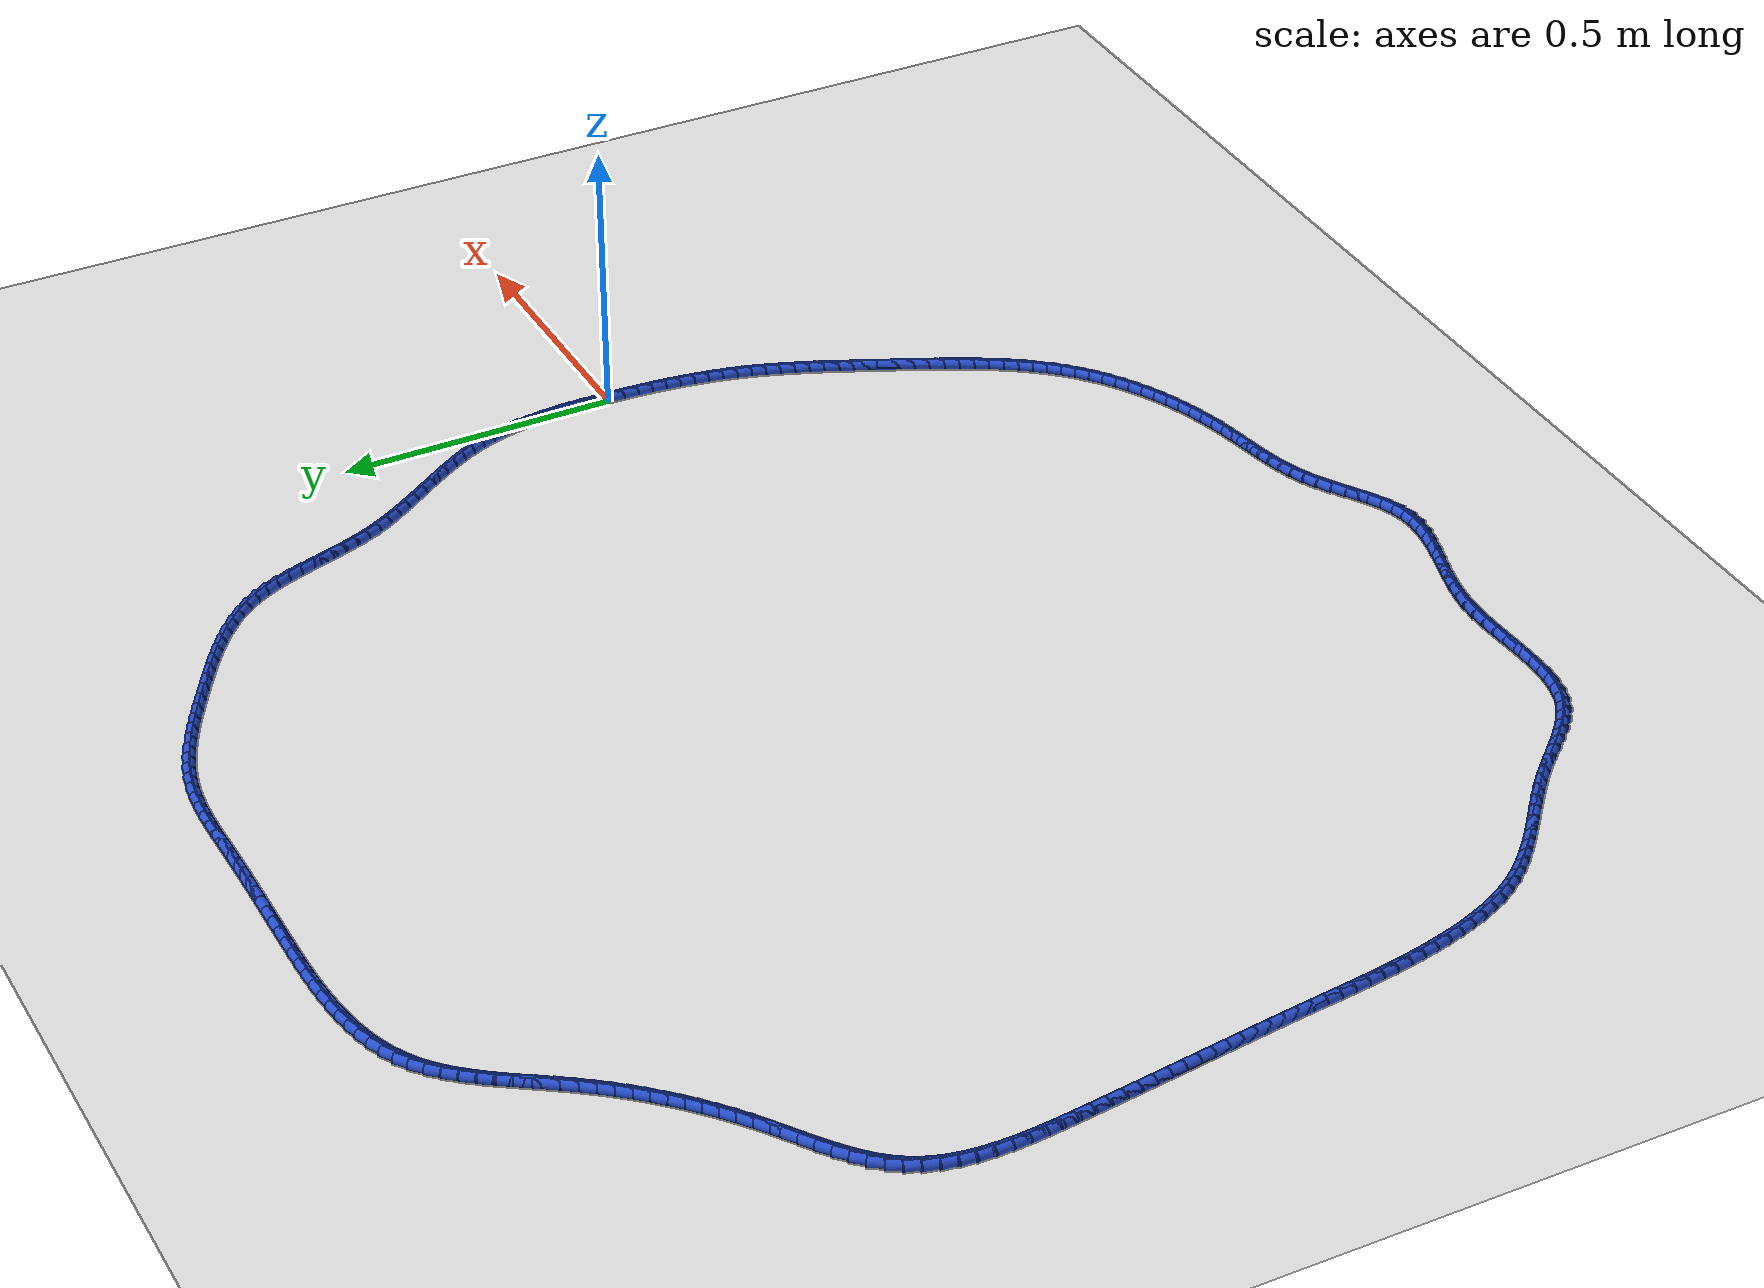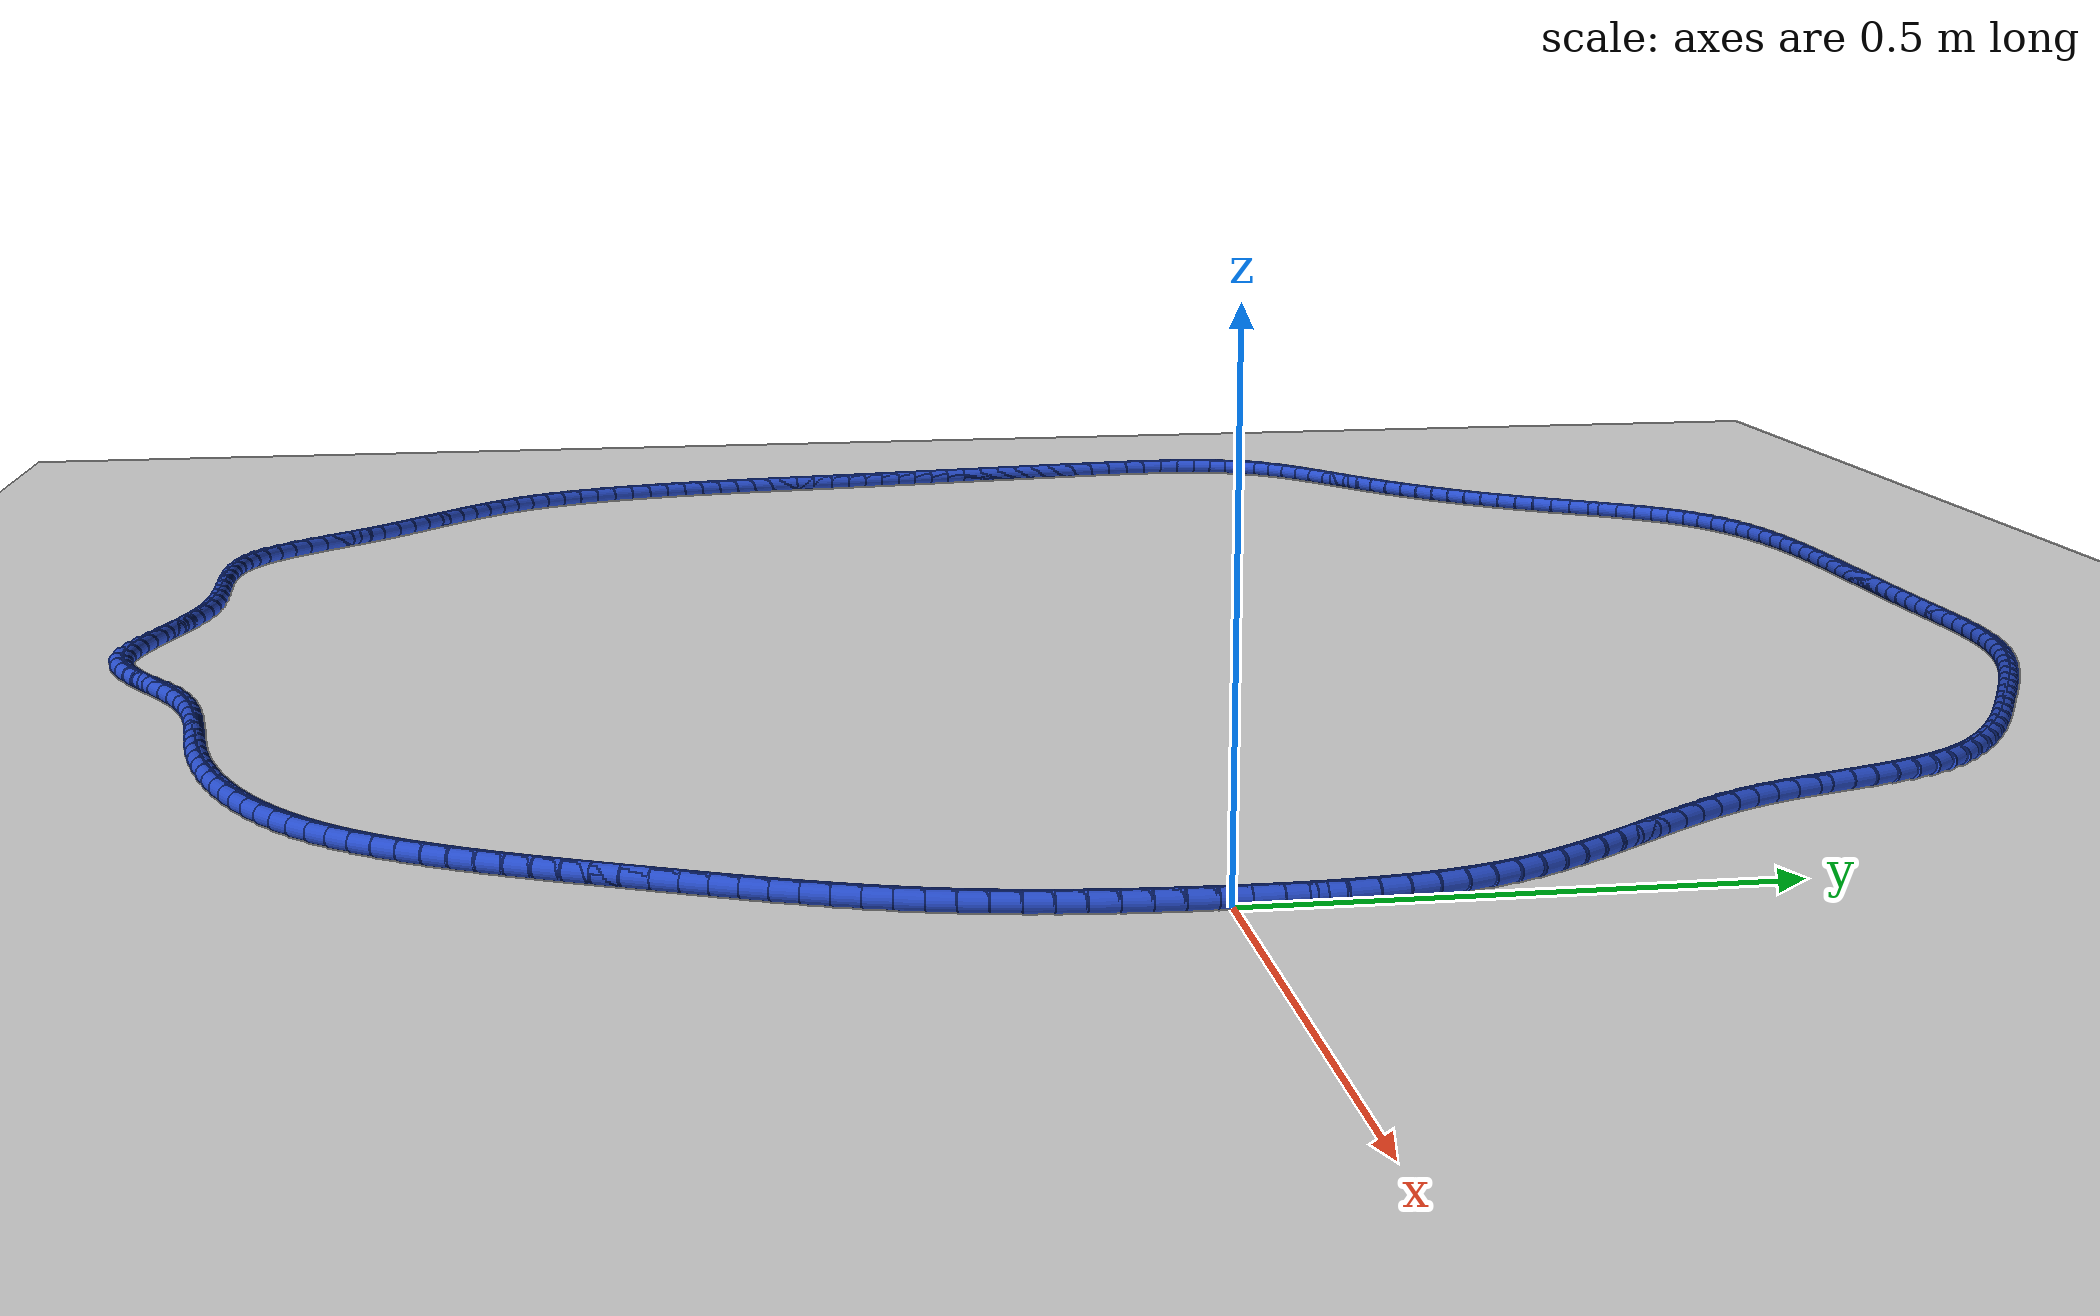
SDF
<sdf version="1.6">
 <world name="default">
  <light name="sun" type="directional">
   <pose>0 0 10 0 -0 0</pose>
   <diffuse>0.8 0.8 0.8 1</diffuse>
   <specular>0.2 0.2 0.2 1</specular>
   <attenuation>
    <range>1000</range>
    <constant>0.9</constant>
    <linear>0.01</linear>
    <quadratic>0.001</quadratic>
   </attenuation>
   <direction>-0.5 0.1 -0.9</direction>
  </light>
  <model name="ground_plane">
   <static>1</static>
   <link name="link">
    <collision name="collision">
     <geometry><plane><normal>0 0 1</normal><size>100 100</size></plane></geometry>
     <surface><friction><ode><mu>100</mu><mu2>50</mu2></ode></friction></surface>
    </collision>
    <visual name="visual">
     <cast_shadows>0</cast_shadows>
     <geometry><plane><normal>0 0 1</normal><size>100 100</size></plane></geometry>
     <material>
      <script><uri>file://media/materials/scripts/gazebo.material</uri><name>Gazebo/WhiteGlow</name></script>
     </material>
    </visual>
   </link>
  </model>
  <gravity>0 0 -9.8</gravity>
  <magnetic_field>6e-06 2.3e-05 -4.2e-05</magnetic_field>
  <atmosphere type="adiabatic"/>
  <physics name="default_physics" default="0" type="ode">
   <max_step_size>0.001</max_step_size>
   <real_time_factor>1</real_time_factor>
   <real_time_update_rate>1000</real_time_update_rate>
  </physics>
  <scene><ambient>0.4 0.4 0.4 1</ambient><background>0.7 0.7 0.7 1</background><shadows>1</shadows></scene>
  <spherical_coordinates>
   <surface_model>EARTH_WGS84</surface_model>
   <latitude_deg>0</latitude_deg>
   <longitude_deg>0</longitude_deg>
   <elevation>0</elevation>
   <heading_deg>0</heading_deg>
  </spherical_coordinates>
  <model name="line">
   <link name="link_0">
    <pose>7.589415207398531e-18 -4.85722573273506e-17 0.01 0 1.57 1.5559141283545928</pose>
    <collision name="collision">
     <geometry><cylinder><radius>0.01</radius><length>0.08</length></cylinder></geometry>
    </collision>
    <visual name="visual">
     <material>
      <script><name>Gazebo/Blue</name><uri>file://media/materials/scripts/gazebo.material</uri></script>
     </material>
     <geometry><cylinder><radius>0.01</radius><length>0.08</length></cylinder></geometry>
    </visual>
   </link>
   <link name="link_1">
    <pose>0.00040557689589350803 0.027250473423718415 0.01 0 1.57 -1.5658515801947306</pose>
    <collision name="collision">
     <geometry><cylinder><radius>0.01</radius><length>0.08</length></cylinder></geometry>
    </collision>
    <visual name="visual">
     <material>
      <script><name>Gazebo/Blue</name><uri>file://media/materials/scripts/gazebo.material</uri></script>
     </material>
     <geometry><cylinder><radius>0.01</radius><length>0.08</length></cylinder></geometry>
    </visual>
   </link>
   <link name="link_2">
    <pose>0.0002706945214770803 0.05452816548895501 0.01 0 1.57 -1.5407802464279325</pose>
    <collision name="collision">
     <geometry><cylinder><radius>0.01</radius><length>0.08</length></cylinder></geometry>
    </collision>
    <visual name="visual">
     <material>
      <script><name>Gazebo/Blue</name><uri>file://media/materials/scripts/gazebo.material</uri></script>
     </material>
     <geometry><cylinder><radius>0.01</radius><length>0.08</length></cylinder></geometry>
    </visual>
   </link>
   <link name="link_3">
    <pose>-0.0005464384559750731 0.08174316324896835 0.01 0 1.57 -1.5102263849374125</pose>
    <collision name="collision">
     <geometry><cylinder><radius>0.01</radius><length>0.08</length></cylinder></geometry>
    </collision>
    <visual name="visual">
     <material>
      <script><name>Gazebo/Blue</name><uri>file://media/materials/scripts/gazebo.material</uri></script>
     </material>
     <geometry><cylinder><radius>0.01</radius><length>0.08</length></cylinder></geometry>
    </visual>
   </link>
   <link name="link_4">
    <pose>-0.0021876133691887483 0.10880555375701705 0.01 0 1.57 -1.4738963994273</pose>
    <collision name="collision">
     <geometry><cylinder><radius>0.01</radius><length>0.08</length></cylinder></geometry>
    </collision>
    <visual name="visual">
     <material>
      <script><name>Gazebo/Blue</name><uri>file://media/materials/scripts/gazebo.material</uri></script>
     </material>
     <geometry><cylinder><radius>0.01</radius><length>0.08</length></cylinder></geometry>
    </visual>
   </link>
   <link name="link_5">
    <pose>-0.004794621550889748 0.1356254240663597 0.01 0 1.57 -1.4314637257471108</pose>
    <collision name="collision">
     <geometry><cylinder><radius>0.01</radius><length>0.08</length></cylinder></geometry>
    </collision>
    <visual name="visual">
     <material>
      <script><name>Gazebo/Blue</name><uri>file://media/materials/scripts/gazebo.material</uri></script>
     </material>
     <geometry><cylinder><radius>0.01</radius><length>0.08</length></cylinder></geometry>
    </visual>
   </link>
   <link name="link_6">
    <pose>-0.008509254333803869 0.16211286123025492 0.01 0 1.57 -1.3826018676959457</pose>
    <collision name="collision">
     <geometry><cylinder><radius>0.01</radius><length>0.08</length></cylinder></geometry>
    </collision>
    <visual name="visual">
     <material>
      <script><name>Gazebo/Blue</name><uri>file://media/materials/scripts/gazebo.material</uri></script>
     </material>
     <geometry><cylinder><radius>0.01</radius><length>0.08</length></cylinder></geometry>
    </visual>
   </link>
   <link name="link_7">
    <pose>-0.013473303050656912 0.1881779523019613 0.01 0 1.57 -1.327031739205355</pose>
    <collision name="collision">
     <geometry><cylinder><radius>0.01</radius><length>0.08</length></cylinder></geometry>
    </collision>
    <visual name="visual">
     <material>
      <script><name>Gazebo/Blue</name><uri>file://media/materials/scripts/gazebo.material</uri></script>
     </material>
     <geometry><cylinder><radius>0.01</radius><length>0.08</length></cylinder></geometry>
    </visual>
   </link>
   <link name="link_8">
    <pose>-0.01982855903417467 0.21373078433473738 0.01 0 1.57 -1.2645858876567104</pose>
    <collision name="collision">
     <geometry><cylinder><radius>0.01</radius><length>0.08</length></cylinder></geometry>
    </collision>
    <visual name="visual">
     <material>
      <script><name>Gazebo/Blue</name><uri>file://media/materials/scripts/gazebo.material</uri></script>
     </material>
     <geometry><cylinder><radius>0.01</radius><length>0.08</length></cylinder></geometry>
    </visual>
   </link>
   <link name="link_9">
    <pose>-0.02771681361708296 0.2386814443818419 0.01 0 1.57 -1.1958644344702418</pose>
    <collision name="collision">
     <geometry><cylinder><radius>0.01</radius><length>0.08</length></cylinder></geometry>
    </collision>
    <visual name="visual">
     <material>
      <script><name>Gazebo/Blue</name><uri>file://media/materials/scripts/gazebo.material</uri></script>
     </material>
     <geometry><cylinder><radius>0.01</radius><length>0.08</length></cylinder></geometry>
    </visual>
   </link>
   <link name="link_10">
    <pose>-0.03726650261467369 0.2629470765192428 0.01 0 1.57 -1.130148149604443</pose>
    <collision name="collision">
     <geometry><cylinder><radius>0.01</radius><length>0.08</length></cylinder></geometry>
    </collision>
    <visual name="visual">
     <material>
      <script><name>Gazebo/Blue</name><uri>file://media/materials/scripts/gazebo.material</uri></script>
     </material>
     <geometry><cylinder><radius>0.01</radius><length>0.08</length></cylinder></geometry>
    </visual>
   </link>
   <link name="link_11">
    <pose>-0.04839899375615982 0.28655423909256245 0.01 0 1.57 -1.074982402908331</pose>
    <collision name="collision">
     <geometry><cylinder><radius>0.01</radius><length>0.08</length></cylinder></geometry>
    </collision>
    <visual name="visual">
     <material>
      <script><name>Gazebo/Blue</name><uri>file://media/materials/scripts/gazebo.material</uri></script>
     </material>
     <geometry><cylinder><radius>0.01</radius><length>0.08</length></cylinder></geometry>
    </visual>
   </link>
   <link name="link_12">
    <pose>-0.060872472729927005 0.3096157154382263 0.01 0 1.57 -1.0307120491372315</pose>
    <collision name="collision">
     <geometry><cylinder><radius>0.01</radius><length>0.08</length></cylinder></geometry>
    </collision>
    <visual name="visual">
     <material>
      <script><name>Gazebo/Blue</name><uri>file://media/materials/scripts/gazebo.material</uri></script>
     </material>
     <geometry><cylinder><radius>0.01</radius><length>0.08</length></cylinder></geometry>
    </visual>
   </link>
   <link name="link_13">
    <pose>-0.074440703302431 0.33224662542537986 0.01 0 1.57 -0.9972079564352885</pose>
    <collision name="collision">
     <geometry><cylinder><radius>0.01</radius><length>0.08</length></cylinder></geometry>
    </collision>
    <visual name="visual">
     <material>
      <script><name>Gazebo/Blue</name><uri>file://media/materials/scripts/gazebo.material</uri></script>
     </material>
     <geometry><cylinder><radius>0.01</radius><length>0.08</length></cylinder></geometry>
    </visual>
   </link>
   <link name="link_14">
    <pose>-0.08885744924012752 0.3545620889231687 0.01 0 1.57 -0.974215683335379</pose>
    <collision name="collision">
     <geometry><cylinder><radius>0.01</radius><length>0.08</length></cylinder></geometry>
    </collision>
    <visual name="visual">
     <material>
      <script><name>Gazebo/Blue</name><uri>file://media/materials/scripts/gazebo.material</uri></script>
     </material>
     <geometry><cylinder><radius>0.01</radius><length>0.08</length></cylinder></geometry>
    </visual>
   </link>
   <link name="link_15">
    <pose>-0.10387647430947233 0.37667722580073837 0.01 0 1.57 -0.9614695580251938</pose>
    <collision name="collision">
     <geometry><cylinder><radius>0.01</radius><length>0.08</length></cylinder></geometry>
    </collision>
    <visual name="visual">
     <material>
      <script><name>Gazebo/Blue</name><uri>file://media/materials/scripts/gazebo.material</uri></script>
     </material>
     <geometry><cylinder><radius>0.01</radius><length>0.08</length></cylinder></geometry>
    </visual>
   </link>
   <link name="link_16">
    <pose>-0.11925154227692127 0.39870715592723444 0.01 0 1.57 -0.9587638180564054</pose>
    <collision name="collision">
     <geometry><cylinder><radius>0.01</radius><length>0.08</length></cylinder></geometry>
    </collision>
    <visual name="visual">
     <material>
      <script><name>Gazebo/Blue</name><uri>file://media/materials/scripts/gazebo.material</uri></script>
     </material>
     <geometry><cylinder><radius>0.01</radius><length>0.08</length></cylinder></geometry>
    </visual>
   </link>
   <link name="link_17">
    <pose>-0.13473641690893007 0.42076699917180266 0.01 0 1.57 -0.9659876066157249</pose>
    <collision name="collision">
     <geometry><cylinder><radius>0.01</radius><length>0.08</length></cylinder></geometry>
    </collision>
    <visual name="visual">
     <material>
      <script><name>Gazebo/Blue</name><uri>file://media/materials/scripts/gazebo.material</uri></script>
     </material>
     <geometry><cylinder><radius>0.01</radius><length>0.08</length></cylinder></geometry>
    </visual>
   </link>
   <link name="link_18">
    <pose>-0.1500848619719544 0.44297187540358834 0.01 0 1.57 -0.9831299147734404</pose>
    <collision name="collision">
     <geometry><cylinder><radius>0.01</radius><length>0.08</length></cylinder></geometry>
    </collision>
    <visual name="visual">
     <material>
      <script><name>Gazebo/Blue</name><uri>file://media/materials/scripts/gazebo.material</uri></script>
     </material>
     <geometry><cylinder><radius>0.01</radius><length>0.08</length></cylinder></geometry>
    </visual>
   </link>
   <link name="link_19">
    <pose>-0.1650506412324501 0.46543690449173725 0.01 0 1.57 -1.0102571729452525</pose>
    <collision name="collision">
     <geometry><cylinder><radius>0.01</radius><length>0.08</length></cylinder></geometry>
    </collision>
    <visual name="visual">
     <material>
      <script><name>Gazebo/Blue</name><uri>file://media/materials/scripts/gazebo.material</uri></script>
     </material>
     <geometry><cylinder><radius>0.01</radius><length>0.08</length></cylinder></geometry>
    </visual>
   </link>
   <link name="link_20">
    <pose>-0.1793875184568729 0.4882772063053949 0.01 0 1.57 -1.0474625991430766</pose>
    <collision name="collision">
     <geometry><cylinder><radius>0.01</radius><length>0.08</length></cylinder></geometry>
    </collision>
    <visual name="visual">
     <material>
      <script><name>Gazebo/Blue</name><uri>file://media/materials/scripts/gazebo.material</uri></script>
     </material>
     <geometry><cylinder><radius>0.01</radius><length>0.08</length></cylinder></geometry>
    </visual>
   </link>
   <link name="link_21">
    <pose>-0.19284925741167855 0.5116079007137067 0.01 0 1.57 -1.0947844968803022</pose>
    <collision name="collision">
     <geometry><cylinder><radius>0.01</radius><length>0.08</length></cylinder></geometry>
    </collision>
    <visual name="visual">
     <material>
      <script><name>Gazebo/Blue</name><uri>file://media/materials/scripts/gazebo.material</uri></script>
     </material>
     <geometry><cylinder><radius>0.01</radius><length>0.08</length></cylinder></geometry>
    </visual>
   </link>
   <link name="link_22">
    <pose>-0.20518962186332285 0.5355441075858185 0.01 0 1.57 -1.15091348865228</pose>
    <collision name="collision">
     <geometry><cylinder><radius>0.01</radius><length>0.08</length></cylinder></geometry>
    </collision>
    <visual name="visual">
     <material>
      <script><name>Gazebo/Blue</name><uri>file://media/materials/scripts/gazebo.material</uri></script>
     </material>
     <geometry><cylinder><radius>0.01</radius><length>0.08</length></cylinder></geometry>
    </visual>
   </link>
   <link name="link_23">
    <pose>-0.21619031697764615 0.560185473931487 0.01 0 1.57 -1.201039827232103</pose>
    <collision name="collision">
     <geometry><cylinder><radius>0.01</radius><length>0.08</length></cylinder></geometry>
    </collision>
    <visual name="visual">
     <material>
      <script><name>Gazebo/Blue</name><uri>file://media/materials/scripts/gazebo.material</uri></script>
     </material>
     <geometry><cylinder><radius>0.01</radius><length>0.08</length></cylinder></geometry>
    </visual>
   </link>
   <link name="link_24">
    <pose>-0.22597864702055695 0.5854402674309478 0.01 0 1.57 -1.2355131958768812</pose>
    <collision name="collision">
     <geometry><cylinder><radius>0.01</radius><length>0.08</length></cylinder></geometry>
    </collision>
    <visual name="visual">
     <material>
      <script><name>Gazebo/Blue</name><uri>file://media/materials/scripts/gazebo.material</uri></script>
     </material>
     <geometry><cylinder><radius>0.01</radius><length>0.08</length></cylinder></geometry>
    </visual>
   </link>
   <link name="link_25">
    <pose>-0.23491516458343212 0.6110875919207465 0.01 0 1.57 -1.2544896879528846</pose>
    <collision name="collision">
     <geometry><cylinder><radius>0.01</radius><length>0.08</length></cylinder></geometry>
    </collision>
    <visual name="visual">
     <material>
      <script><name>Gazebo/Blue</name><uri>file://media/materials/scripts/gazebo.material</uri></script>
     </material>
     <geometry><cylinder><radius>0.01</radius><length>0.08</length></cylinder></geometry>
    </visual>
   </link>
   <link name="link_26">
    <pose>-0.24336479887652204 0.636904127636252 0.01 0 1.57 -1.2581489119808016</pose>
    <collision name="collision">
     <geometry><cylinder><radius>0.01</radius><length>0.08</length></cylinder></geometry>
    </collision>
    <visual name="visual">
     <material>
      <script><name>Gazebo/Blue</name><uri>file://media/materials/scripts/gazebo.material</uri></script>
     </material>
     <geometry><cylinder><radius>0.01</radius><length>0.08</length></cylinder></geometry>
    </visual>
   </link>
   <link name="link_27">
    <pose>-0.25169247911007714 0.6626665548128341 0.01 0 1.57 -1.2463763810399993</pose>
    <collision name="collision">
     <geometry><cylinder><radius>0.01</radius><length>0.08</length></cylinder></geometry>
    </collision>
    <visual name="visual">
     <material>
      <script><name>Gazebo/Blue</name><uri>file://media/materials/scripts/gazebo.material</uri></script>
     </material>
     <geometry><cylinder><radius>0.01</radius><length>0.08</length></cylinder></geometry>
    </visual>
   </link>
   <link name="link_28">
    <pose>-0.2602631344943479 0.6881515536858619 0.01 0 1.57 -1.2187283245380092</pose>
    <collision name="collision">
     <geometry><cylinder><radius>0.01</radius><length>0.08</length></cylinder></geometry>
    </collision>
    <visual name="visual">
     <material>
      <script><name>Gazebo/Blue</name><uri>file://media/materials/scripts/gazebo.material</uri></script>
     </material>
     <geometry><cylinder><radius>0.01</radius><length>0.08</length></cylinder></geometry>
    </visual>
   </link>
   <link name="link_29">
    <pose>-0.2694416942395844 0.7131358044907046 0.01 0 1.57 -1.174496473592519</pose>
    <collision name="collision">
     <geometry><cylinder><radius>0.01</radius><length>0.08</length></cylinder></geometry>
    </collision>
    <visual name="visual">
     <material>
      <script><name>Gazebo/Blue</name><uri>file://media/materials/scripts/gazebo.material</uri></script>
     </material>
     <geometry><cylinder><radius>0.01</radius><length>0.08</length></cylinder></geometry>
    </visual>
   </link>
   <link name="link_30">
    <pose>-0.27959308755603707 0.737395987462731 0.01 0 1.57 -1.1129042188250629</pose>
    <collision name="collision">
     <geometry><cylinder><radius>0.01</radius><length>0.08</length></cylinder></geometry>
    </collision>
    <visual name="visual">
     <material>
      <script><name>Gazebo/Blue</name><uri>file://media/materials/scripts/gazebo.material</uri></script>
     </material>
     <geometry><cylinder><radius>0.01</radius><length>0.08</length></cylinder></geometry>
    </visual>
   </link>
   <link name="link_31">
    <pose>-0.2910822436539564 0.760708782837311 0.01 0 1.57 -1.0334855148487176</pose>
    <collision name="collision">
     <geometry><cylinder><radius>0.01</radius><length>0.08</length></cylinder></geometry>
    </collision>
    <visual name="visual">
     <material>
      <script><name>Gazebo/Blue</name><uri>file://media/materials/scripts/gazebo.material</uri></script>
     </material>
     <geometry><cylinder><radius>0.01</radius><length>0.08</length></cylinder></geometry>
    </visual>
   </link>
   <link name="link_32">
    <pose>-0.30427406672204727 0.7828508858808201 0.01 0 1.57 -0.941879065706948</pose>
    <collision name="collision">
     <geometry><cylinder><radius>0.01</radius><length>0.08</length></cylinder></geometry>
    </collision>
    <visual name="visual">
     <material>
      <script><name>Gazebo/Blue</name><uri>file://media/materials/scripts/gazebo.material</uri></script>
     </material>
     <geometry><cylinder><radius>0.01</radius><length>0.08</length></cylinder></geometry>
    </visual>
   </link>
   <link name="link_33">
    <pose>-0.3194179253571463 0.803668396692331 0.01 0 1.57 -0.856585667237983</pose>
    <collision name="collision">
     <geometry><cylinder><radius>0.01</radius><length>0.08</length></cylinder></geometry>
    </collision>
    <visual name="visual">
     <material>
      <script><name>Gazebo/Blue</name><uri>file://media/materials/scripts/gazebo.material</uri></script>
     </material>
     <geometry><cylinder><radius>0.01</radius><length>0.08</length></cylinder></geometry>
    </visual>
   </link>
   <link name="link_34">
    <pose>-0.3363813264708986 0.8232368082873882 0.01 0 1.57 -0.7818985462586857</pose>
    <collision name="collision">
     <geometry><cylinder><radius>0.01</radius><length>0.08</length></cylinder></geometry>
    </collision>
    <visual name="visual">
     <material>
      <script><name>Gazebo/Blue</name><uri>file://media/materials/scripts/gazebo.material</uri></script>
     </material>
     <geometry><cylinder><radius>0.01</radius><length>0.08</length></cylinder></geometry>
    </visual>
   </link>
   <link name="link_35">
    <pose>-0.3549529935180553 0.841678940678841 0.01 0 1.57 -0.717867649920996</pose>
    <collision name="collision">
     <geometry><cylinder><radius>0.01</radius><length>0.08</length></cylinder></geometry>
    </collision>
    <visual name="visual">
     <material>
      <script><name>Gazebo/Blue</name><uri>file://media/materials/scripts/gazebo.material</uri></script>
     </material>
     <geometry><cylinder><radius>0.01</radius><length>0.08</length></cylinder></geometry>
    </visual>
   </link>
   <link name="link_36">
    <pose>-0.374921649953368 0.8591176138795393 0.01 0 1.57 -0.6641177099415944</pose>
    <collision name="collision">
     <geometry><cylinder><radius>0.01</radius><length>0.08</length></cylinder></geometry>
    </collision>
    <visual name="visual">
     <material>
      <script><name>Gazebo/Blue</name><uri>file://media/materials/scripts/gazebo.material</uri></script>
     </material>
     <geometry><cylinder><radius>0.01</radius><length>0.08</length></cylinder></geometry>
    </visual>
   </link>
   <link name="link_37">
    <pose>-0.39607601923158775 0.8756756479023325 0.01 0 1.57 -0.6200676844374162</pose>
    <collision name="collision">
     <geometry><cylinder><radius>0.01</radius><length>0.08</length></cylinder></geometry>
    </collision>
    <visual name="visual">
     <material>
      <script><name>Gazebo/Blue</name><uri>file://media/materials/scripts/gazebo.material</uri></script>
     </material>
     <geometry><cylinder><radius>0.01</radius><length>0.08</length></cylinder></geometry>
    </visual>
   </link>
   <link name="link_38">
    <pose>-0.4182048248074661 0.8914758627600707 0.01 0 1.57 -0.5850908429274463</pose>
    <collision name="collision">
     <geometry><cylinder><radius>0.01</radius><length>0.08</length></cylinder></geometry>
    </collision>
    <visual name="visual">
     <material>
      <script><name>Gazebo/Blue</name><uri>file://media/materials/scripts/gazebo.material</uri></script>
     </material>
     <geometry><cylinder><radius>0.01</radius><length>0.08</length></cylinder></geometry>
    </visual>
   </link>
   <link name="link_39">
    <pose>-0.4410967901357544 0.9066410784656037 0.01 0 1.57 -0.5586186770879736</pose>
    <collision name="collision">
     <geometry><cylinder><radius>0.01</radius><length>0.08</length></cylinder></geometry>
    </collision>
    <visual name="visual">
     <material>
      <script><name>Gazebo/Blue</name><uri>file://media/materials/scripts/gazebo.material</uri></script>
     </material>
     <geometry><cylinder><radius>0.01</radius><length>0.08</length></cylinder></geometry>
    </visual>
   </link>
   <link name="link_40">
    <pose>-0.4645406386712038 0.921294115031781 0.01 0 1.57 -0.5402032014789102</pose>
    <collision name="collision">
     <geometry><cylinder><radius>0.01</radius><length>0.08</length></cylinder></geometry>
    </collision>
    <visual name="visual">
     <material>
      <script><name>Gazebo/Blue</name><uri>file://media/materials/scripts/gazebo.material</uri></script>
     </material>
     <geometry><cylinder><radius>0.01</radius><length>0.08</length></cylinder></geometry>
    </visual>
   </link>
   <link name="link_41">
    <pose>-0.4883250938685658 0.9355577924714523 0.01 0 1.57 -0.529553001777052</pose>
    <collision name="collision">
     <geometry><cylinder><radius>0.01</radius><length>0.08</length></cylinder></geometry>
    </collision>
    <visual name="visual">
     <material>
      <script><name>Gazebo/Blue</name><uri>file://media/materials/scripts/gazebo.material</uri></script>
     </material>
     <geometry><cylinder><radius>0.01</radius><length>0.08</length></cylinder></geometry>
    </visual>
   </link>
   <link name="link_42">
    <pose>-0.5122388791825916 0.9495549307974676 0.01 0 1.57 -0.5244024457779427</pose>
    <collision name="collision">
     <geometry><cylinder><radius>0.01</radius><length>0.08</length></cylinder></geometry>
    </collision>
    <visual name="visual">
     <material>
      <script><name>Gazebo/Blue</name><uri>file://media/materials/scripts/gazebo.material</uri></script>
     </material>
     <geometry><cylinder><radius>0.01</radius><length>0.08</length></cylinder></geometry>
    </visual>
   </link>
   <link name="link_43">
    <pose>-0.5361121660268895 0.9633637729293281 0.01 0 1.57 -0.5153416954355567</pose>
    <collision name="collision">
     <geometry><cylinder><radius>0.01</radius><length>0.08</length></cylinder></geometry>
    </collision>
    <visual name="visual">
     <material>
      <script><name>Gazebo/Blue</name><uri>file://media/materials/scripts/gazebo.material</uri></script>
     </material>
     <geometry><cylinder><radius>0.01</radius><length>0.08</length></cylinder></geometry>
    </visual>
   </link>
   <link name="link_44">
    <pose>-0.559955563430595 0.9768685019425114 0.01 0 1.57 -0.4996777532496306</pose>
    <collision name="collision">
     <geometry><cylinder><radius>0.01</radius><length>0.08</length></cylinder></geometry>
    </collision>
    <visual name="visual">
     <material>
      <script><name>Gazebo/Blue</name><uri>file://media/materials/scripts/gazebo.material</uri></script>
     </material>
     <geometry><cylinder><radius>0.01</radius><length>0.08</length></cylinder></geometry>
    </visual>
   </link>
   <link name="link_45">
    <pose>-0.5838287690339036 0.9899005063320652 0.01 0 1.57 -0.47721897277248393</pose>
    <collision name="collision">
     <geometry><cylinder><radius>0.01</radius><length>0.08</length></cylinder></geometry>
    </collision>
    <visual name="visual">
     <material>
      <script><name>Gazebo/Blue</name><uri>file://media/materials/scripts/gazebo.material</uri></script>
     </material>
     <geometry><cylinder><radius>0.01</radius><length>0.08</length></cylinder></geometry>
    </visual>
   </link>
   <link name="link_46">
    <pose>-0.6077914814902828 1.0022911735032665 0.01 0 1.57 -0.4477557884236894</pose>
    <collision name="collision">
     <geometry><cylinder><radius>0.01</radius><length>0.08</length></cylinder></geometry>
    </collision>
    <visual name="visual">
     <material>
      <script><name>Gazebo/Blue</name><uri>file://media/materials/scripts/gazebo.material</uri></script>
     </material>
     <geometry><cylinder><radius>0.01</radius><length>0.08</length></cylinder></geometry>
    </visual>
   </link>
   <link name="link_47">
    <pose>-0.6319033994532005 1.0138718908613922 0.01 0 1.57 -0.41109118482752866</pose>
    <collision name="collision">
     <geometry><cylinder><radius>0.01</radius><length>0.08</length></cylinder></geometry>
    </collision>
    <visual name="visual">
     <material>
      <script><name>Gazebo/Blue</name><uri>file://media/materials/scripts/gazebo.material</uri></script>
     </material>
     <geometry><cylinder><radius>0.01</radius><length>0.08</length></cylinder></geometry>
    </visual>
   </link>
   <link name="link_48">
    <pose>-0.6562242215761251 1.0244740458117199 0.01 0 1.57 -0.36708557528060404</pose>
    <collision name="collision">
     <geometry><cylinder><radius>0.01</radius><length>0.08</length></cylinder></geometry>
    </collision>
    <visual name="visual">
     <material>
      <script><name>Gazebo/Blue</name><uri>file://media/materials/scripts/gazebo.material</uri></script>
     </material>
     <geometry><cylinder><radius>0.01</radius><length>0.08</length></cylinder></geometry>
    </visual>
   </link>
   <link name="link_49">
    <pose>-0.6808136465125245 1.0339290257595262 0.01 0 1.57 -0.31571690771805666</pose>
    <collision name="collision">
     <geometry><cylinder><radius>0.01</radius><length>0.08</length></cylinder></geometry>
    </collision>
    <visual name="visual">
     <material>
      <script><name>Gazebo/Blue</name><uri>file://media/materials/scripts/gazebo.material</uri></script>
     </material>
     <geometry><cylinder><radius>0.01</radius><length>0.08</length></cylinder></geometry>
    </visual>
   </link>
   <link name="link_50">
    <pose>-0.7057313729158664 1.0420682181100882 0.01 0 1.57 -0.257153350176507</pose>
    <collision name="collision">
     <geometry><cylinder><radius>0.01</radius><length>0.08</length></cylinder></geometry>
    </collision>
    <visual name="visual">
     <material>
      <script><name>Gazebo/Blue</name><uri>file://media/materials/scripts/gazebo.material</uri></script>
     </material>
     <geometry><cylinder><radius>0.01</radius><length>0.08</length></cylinder></geometry>
    </visual>
   </link>
   <link name="link_51">
    <pose>-0.7310370994396191 1.048723010268683 0.01 0 1.57 -0.19238497160615148</pose>
    <collision name="collision">
     <geometry><cylinder><radius>0.01</radius><length>0.08</length></cylinder></geometry>
    </collision>
    <visual name="visual">
     <material>
      <script><name>Gazebo/Blue</name><uri>file://media/materials/scripts/gazebo.material</uri></script>
     </material>
     <geometry><cylinder><radius>0.01</radius><length>0.08</length></cylinder></geometry>
    </visual>
   </link>
   <link name="link_52">
    <pose>-0.7567856003676122 1.0537386679174294 0.01 0 1.57 -0.13102034681749103</pose>
    <collision name="collision">
     <geometry><cylinder><radius>0.01</radius><length>0.08</length></cylinder></geometry>
    </collision>
    <visual name="visual">
     <material>
      <script><name>Gazebo/Blue</name><uri>file://media/materials/scripts/gazebo.material</uri></script>
     </material>
     <geometry><cylinder><radius>0.01</radius><length>0.08</length></cylinder></geometry>
    </visual>
   </link>
   <link name="link_53">
    <pose>-0.7829513835665042 1.0571866703739625 0.01 0 1.57 -0.08045230609169367</pose>
    <collision name="collision">
     <geometry><cylinder><radius>0.01</radius><length>0.08</length></cylinder></geometry>
    </collision>
    <visual name="visual">
     <material>
      <script><name>Gazebo/Blue</name><uri>file://media/materials/scripts/gazebo.material</uri></script>
     </material>
     <geometry><cylinder><radius>0.01</radius><length>0.08</length></cylinder></geometry>
    </visual>
   </link>
   <link name="link_54">
    <pose>-0.8094436174735646 1.0593226420864252 0.01 0 1.57 -0.04057190371846167</pose>
    <collision name="collision">
     <geometry><cylinder><radius>0.01</radius><length>0.08</length></cylinder></geometry>
    </collision>
    <visual name="visual">
     <material>
      <script><name>Gazebo/Blue</name><uri>file://media/materials/scripts/gazebo.material</uri></script>
     </material>
     <geometry><cylinder><radius>0.01</radius><length>0.08</length></cylinder></geometry>
    </visual>
   </link>
   <link name="link_55">
    <pose>-0.8361695712296399 1.0604075602614795 0.01 0 1.57 -0.010973708911569565</pose>
    <collision name="collision">
     <geometry><cylinder><radius>0.01</radius><length>0.08</length></cylinder></geometry>
    </collision>
    <visual name="visual">
     <material>
      <script><name>Gazebo/Blue</name><uri>file://media/materials/scripts/gazebo.material</uri></script>
     </material>
     <geometry><cylinder><radius>0.01</radius><length>0.08</length></cylinder></geometry>
    </visual>
   </link>
   <link name="link_56">
    <pose>-0.8630365139755777 1.0607024021057887 0.01 0 1.57 0.008703311040011917</pose>
    <collision name="collision">
     <geometry><cylinder><radius>0.01</radius><length>0.08</length></cylinder></geometry>
    </collision>
    <visual name="visual">
     <material>
      <script><name>Gazebo/Blue</name><uri>file://media/materials/scripts/gazebo.material</uri></script>
     </material>
     <geometry><cylinder><radius>0.01</radius><length>0.08</length></cylinder></geometry>
    </visual>
   </link>
   <link name="link_57">
    <pose>-0.889951714852225 1.0604681448260143 0.01 0 1.57 0.01869397330084533</pose>
    <collision name="collision">
     <geometry><cylinder><radius>0.01</radius><length>0.08</length></cylinder></geometry>
    </collision>
    <visual name="visual">
     <material>
      <script><name>Gazebo/Blue</name><uri>file://media/materials/scripts/gazebo.material</uri></script>
     </material>
     <geometry><cylinder><radius>0.01</radius><length>0.08</length></cylinder></geometry>
    </visual>
   </link>
   <link name="link_58">
    <pose>-0.9168224430004293 1.0599657656288193 0.01 0 1.57 0.019061448312469573</pose>
    <collision name="collision">
     <geometry><cylinder><radius>0.01</radius><length>0.08</length></cylinder></geometry>
    </collision>
    <visual name="visual">
     <material>
      <script><name>Gazebo/Blue</name><uri>file://media/materials/scripts/gazebo.material</uri></script>
     </material>
     <geometry><cylinder><radius>0.01</radius><length>0.08</length></cylinder></geometry>
    </visual>
   </link>
   <link name="link_59">
    <pose>-0.9435560314435383 1.0594561229886919 0.01 0 1.57 0.01235893265124324</pose>
    <collision name="collision">
     <geometry><cylinder><radius>0.01</radius><length>0.08</length></cylinder></geometry>
    </collision>
    <visual name="visual">
     <material>
      <script><name>Gazebo/Blue</name><uri>file://media/materials/scripts/gazebo.material</uri></script>
     </material>
     <geometry><cylinder><radius>0.01</radius><length>0.08</length></cylinder></geometry>
    </visual>
   </link>
   <link name="link_60">
    <pose>-0.9700985554113428 1.0591280690197369 0.01 0 1.57 0.005743622762257811</pose>
    <collision name="collision">
     <geometry><cylinder><radius>0.01</radius><length>0.08</length></cylinder></geometry>
    </collision>
    <visual name="visual">
     <material>
      <script><name>Gazebo/Blue</name><uri>file://media/materials/scripts/gazebo.material</uri></script>
     </material>
     <geometry><cylinder><radius>0.01</radius><length>0.08</length></cylinder></geometry>
    </visual>
   </link>
   <link name="link_61">
    <pose>-0.9965004864311326 1.0589764246202178 0.01 0 1.57 0.0004848784744612575</pose>
    <collision name="collision">
     <geometry><cylinder><radius>0.01</radius><length>0.08</length></cylinder></geometry>
    </collision>
    <visual name="visual">
     <material>
      <script><name>Gazebo/Blue</name><uri>file://media/materials/scripts/gazebo.material</uri></script>
     </material>
     <geometry><cylinder><radius>0.01</radius><length>0.08</length></cylinder></geometry>
    </visual>
   </link>
   <link name="link_62">
    <pose>-1.0228297029475633 1.058963658148879 0.01 0 1.57 -0.003364921784448303</pose>
    <collision name="collision">
     <geometry><cylinder><radius>0.01</radius><length>0.08</length></cylinder></geometry>
    </collision>
    <visual name="visual">
     <material>
      <script><name>Gazebo/Blue</name><uri>file://media/materials/scripts/gazebo.material</uri></script>
     </material>
     <geometry><cylinder><radius>0.01</radius><length>0.08</length></cylinder></geometry>
    </visual>
   </link>
   <link name="link_63">
    <pose>-1.0491540834052888 1.0590522379644645 0.01 0 1.57 -0.005775204645112924</pose>
    <collision name="collision">
     <geometry><cylinder><radius>0.01</radius><length>0.08</length></cylinder></geometry>
    </collision>
    <visual name="visual">
     <material>
      <script><name>Gazebo/Blue</name><uri>file://media/materials/scripts/gazebo.material</uri></script>
     </material>
     <geometry><cylinder><radius>0.01</radius><length>0.08</length></cylinder></geometry>
    </visual>
   </link>
   <link name="link_64">
    <pose>-1.0755415062489644 1.0592046324257178 0.01 0 1.57 -0.006737779855519012</pose>
    <collision name="collision">
     <geometry><cylinder><radius>0.01</radius><length>0.08</length></cylinder></geometry>
    </collision>
    <visual name="visual">
     <material>
      <script><name>Gazebo/Blue</name><uri>file://media/materials/scripts/gazebo.material</uri></script>
     </material>
     <geometry><cylinder><radius>0.01</radius><length>0.08</length></cylinder></geometry>
    </visual>
   </link>
   <link name="link_65">
    <pose>-1.1020598499232457 1.0593833098913836 0.01 0 1.57 -0.006266637022066119</pose>
    <collision name="collision">
     <geometry><cylinder><radius>0.01</radius><length>0.08</length></cylinder></geometry>
    </collision>
    <visual name="visual">
     <material>
      <script><name>Gazebo/Blue</name><uri>file://media/materials/scripts/gazebo.material</uri></script>
     </material>
     <geometry><cylinder><radius>0.01</radius><length>0.08</length></cylinder></geometry>
    </visual>
   </link>
   <link name="link_66">
    <pose>-1.1287769928727875 1.0595507387202054 0.01 0 1.57 -0.004396997279999154</pose>
    <collision name="collision">
     <geometry><cylinder><radius>0.01</radius><length>0.08</length></cylinder></geometry>
    </collision>
    <visual name="visual">
     <material>
      <script><name>Gazebo/Blue</name><uri>file://media/materials/scripts/gazebo.material</uri></script>
     </material>
     <geometry><cylinder><radius>0.01</radius><length>0.08</length></cylinder></geometry>
    </visual>
   </link>
   <link name="link_67">
    <pose>-1.1557608135422444 1.059669387270928 0.01 0 1.57 -0.0011836946411880468</pose>
    <collision name="collision">
     <geometry><cylinder><radius>0.01</radius><length>0.08</length></cylinder></geometry>
    </collision>
    <visual name="visual">
     <material>
      <script><name>Gazebo/Blue</name><uri>file://media/materials/scripts/gazebo.material</uri></script>
     </material>
     <geometry><cylinder><radius>0.01</radius><length>0.08</length></cylinder></geometry>
    </visual>
   </link>
   <link name="link_68">
    <pose>-1.1830791903762718 1.059701723902295 0.01 0 1.57 0.003604888886453969</pose>
    <collision name="collision">
     <geometry><cylinder><radius>0.01</radius><length>0.08</length></cylinder></geometry>
    </collision>
    <visual name="visual">
     <material>
      <script><name>Gazebo/Blue</name><uri>file://media/materials/scripts/gazebo.material</uri></script>
     </material>
     <geometry><cylinder><radius>0.01</radius><length>0.08</length></cylinder></geometry>
    </visual>
   </link>
   <link name="link_69">
    <pose>-1.2107855100429812 1.0596018452657952 0.01 0 1.57 0.012696967394361788</pose>
    <collision name="collision">
     <geometry><cylinder><radius>0.01</radius><length>0.08</length></cylinder></geometry>
    </collision>
    <visual name="visual">
     <material>
      <script><name>Gazebo/Blue</name><uri>file://media/materials/scripts/gazebo.material</uri></script>
     </material>
     <geometry><cylinder><radius>0.01</radius><length>0.08</length></cylinder></geometry>
    </visual>
   </link>
   <link name="link_70">
    <pose>-1.2387986506805304 1.059246144217759 0.01 0 1.57 0.02758980661236838</pose>
    <collision name="collision">
     <geometry><cylinder><radius>0.01</radius><length>0.08</length></cylinder></geometry>
    </collision>
    <visual name="visual">
     <material>
      <script><name>Gazebo/Blue</name><uri>file://media/materials/scripts/gazebo.material</uri></script>
     </material>
     <geometry><cylinder><radius>0.01</radius><length>0.08</length></cylinder></geometry>
    </visual>
   </link>
   <link name="link_71">
    <pose>-1.266964514268925 1.0584688562550761 0.01 0 1.57 0.04843066377440096</pose>
    <collision name="collision">
     <geometry><cylinder><radius>0.01</radius><length>0.08</length></cylinder></geometry>
    </collision>
    <visual name="visual">
     <material>
      <script><name>Gazebo/Blue</name><uri>file://media/materials/scripts/gazebo.material</uri></script>
     </material>
     <geometry><cylinder><radius>0.01</radius><length>0.08</length></cylinder></geometry>
    </visual>
   </link>
   <link name="link_72">
    <pose>-1.2951282794080345 1.057103798987522 0.01 0 1.57 0.07551651580947118</pose>
    <collision name="collision">
     <geometry><cylinder><radius>0.01</radius><length>0.08</length></cylinder></geometry>
    </collision>
    <visual name="visual">
     <material>
      <script><name>Gazebo/Blue</name><uri>file://media/materials/scripts/gazebo.material</uri></script>
     </material>
     <geometry><cylinder><radius>0.01</radius><length>0.08</length></cylinder></geometry>
    </visual>
   </link>
   <link name="link_73">
    <pose>-1.3231351246977294 1.0549847900248703 0.01 0 1.57 0.1092984297215012</pose>
    <collision name="collision">
     <geometry><cylinder><radius>0.01</radius><length>0.08</length></cylinder></geometry>
    </collision>
    <visual name="visual">
     <material>
      <script><name>Gazebo/Blue</name><uri>file://media/materials/scripts/gazebo.material</uri></script>
     </material>
     <geometry><cylinder><radius>0.01</radius><length>0.08</length></cylinder></geometry>
    </visual>
   </link>
   <link name="link_74">
    <pose>-1.3508302287378797 1.0519456469768942 0.01 0 1.57 0.15036866173066032</pose>
    <collision name="collision">
     <geometry><cylinder><radius>0.01</radius><length>0.08</length></cylinder></geometry>
    </collision>
    <visual name="visual">
     <material>
      <script><name>Gazebo/Blue</name><uri>file://media/materials/scripts/gazebo.material</uri></script>
     </material>
     <geometry><cylinder><radius>0.01</radius><length>0.08</length></cylinder></geometry>
    </visual>
   </link>
   <link name="link_75">
    <pose>-1.3780587701283553 1.0478201874533686 0.01 0 1.57 0.19943751177327446</pose>
    <collision name="collision">
     <geometry><cylinder><radius>0.01</radius><length>0.08</length></cylinder></geometry>
    </collision>
    <visual name="visual">
     <material>
      <script><name>Gazebo/Blue</name><uri>file://media/materials/scripts/gazebo.material</uri></script>
     </material>
     <geometry><cylinder><radius>0.01</radius><length>0.08</length></cylinder></geometry>
    </visual>
   </link>
   <link name="link_76">
    <pose>-1.404665927469026 1.042442229064067 0.01 0 1.57 0.25728825915736203</pose>
    <collision name="collision">
     <geometry><cylinder><radius>0.01</radius><length>0.08</length></cylinder></geometry>
    </collision>
    <visual name="visual">
     <material>
      <script><name>Gazebo/Blue</name><uri>file://media/materials/scripts/gazebo.material</uri></script>
     </material>
     <geometry><cylinder><radius>0.01</radius><length>0.08</length></cylinder></geometry>
    </visual>
   </link>
   <link name="link_77">
    <pose>-1.4304968793597614 1.0356455894187633 0.01 0 1.57 0.324694468260515</pose>
    <collision name="collision">
     <geometry><cylinder><radius>0.01</radius><length>0.08</length></cylinder></geometry>
    </collision>
    <visual name="visual">
     <material>
      <script><name>Gazebo/Blue</name><uri>file://media/materials/scripts/gazebo.material</uri></script>
     </material>
     <geometry><cylinder><radius>0.01</radius><length>0.08</length></cylinder></geometry>
    </visual>
   </link>
   <link name="link_78">
    <pose>-1.4553968044004317 1.0272640861272313 0.01 0 1.57 0.40228197470333926</pose>
    <collision name="collision">
     <geometry><cylinder><radius>0.01</radius><length>0.08</length></cylinder></geometry>
    </collision>
    <visual name="visual">
     <material>
      <script><name>Gazebo/Blue</name><uri>file://media/materials/scripts/gazebo.material</uri></script>
     </material>
     <geometry><cylinder><radius>0.01</radius><length>0.08</length></cylinder></geometry>
    </visual>
   </link>
   <link name="link_79">
    <pose>-1.4792108811909075 1.0171315367992455 0.01 0 1.57 0.4903237847307311</pose>
    <collision name="collision">
     <geometry><cylinder><radius>0.01</radius><length>0.08</length></cylinder></geometry>
    </collision>
    <visual name="visual">
     <material>
      <script><name>Gazebo/Blue</name><uri>file://media/materials/scripts/gazebo.material</uri></script>
     </material>
     <geometry><cylinder><radius>0.01</radius><length>0.08</length></cylinder></geometry>
    </visual>
   </link>
   <link name="link_80">
    <pose>-1.501784288331058 1.0050817590445793 0.01 0 1.57 0.5884790030276664</pose>
    <collision name="collision">
     <geometry><cylinder><radius>0.01</radius><length>0.08</length></cylinder></geometry>
    </collision>
    <visual name="visual">
     <material>
      <script><name>Gazebo/Blue</name><uri>file://media/materials/scripts/gazebo.material</uri></script>
     </material>
     <geometry><cylinder><radius>0.01</radius><length>0.08</length></cylinder></geometry>
    </visual>
   </link>
   <link name="link_81">
    <pose>-1.522962204420753 0.9909485704730067 0.01 0 1.57 0.6923813892779749</pose>
    <collision name="collision">
     <geometry><cylinder><radius>0.01</radius><length>0.08</length></cylinder></geometry>
    </collision>
    <visual name="visual">
     <material>
      <script><name>Gazebo/Blue</name><uri>file://media/materials/scripts/gazebo.material</uri></script>
     </material>
     <geometry><cylinder><radius>0.01</radius><length>0.08</length></cylinder></geometry>
    </visual>
   </link>
   <link name="link_82">
    <pose>-1.5426389905982425 0.974629676253857 0.01 0 1.57 0.7837659272731945</pose>
    <collision name="collision">
     <geometry><cylinder><radius>0.01</radius><length>0.08</length></cylinder></geometry>
    </collision>
    <visual name="visual">
     <material>
      <script><name>Gazebo/Blue</name><uri>file://media/materials/scripts/gazebo.material</uri></script>
     </material>
     <geometry><cylinder><radius>0.01</radius><length>0.08</length></cylinder></geometry>
    </visual>
   </link>
   <link name="link_83">
    <pose>-1.5609685204088002 0.9563598852299404 0.01 0 1.57 0.856810654508606</pose>
    <collision name="collision">
     <geometry><cylinder><radius>0.01</radius><length>0.08</length></cylinder></geometry>
    </collision>
    <visual name="visual">
     <material>
      <script><name>Gazebo/Blue</name><uri>file://media/materials/scripts/gazebo.material</uri></script>
     </material>
     <geometry><cylinder><radius>0.01</radius><length>0.08</length></cylinder></geometry>
    </visual>
   </link>
   <link name="link_84">
    <pose>-1.578189950123699 0.936484787537914 0.01 0 1.57 0.9122817195660957</pose>
    <collision name="collision">
     <geometry><cylinder><radius>0.01</radius><length>0.08</length></cylinder></geometry>
    </collision>
    <visual name="visual">
     <material>
      <script><name>Gazebo/Blue</name><uri>file://media/materials/scripts/gazebo.material</uri></script>
     </material>
     <geometry><cylinder><radius>0.01</radius><length>0.08</length></cylinder></geometry>
    </visual>
   </link>
   <link name="link_85">
    <pose>-1.594542486946457 0.9153500394748432 0.01 0 1.57 0.9513356298603579</pose>
    <collision name="collision">
     <geometry><cylinder><radius>0.01</radius><length>0.08</length></cylinder></geometry>
    </collision>
    <visual name="visual">
     <material>
      <script><name>Gazebo/Blue</name><uri>file://media/materials/scripts/gazebo.material</uri></script>
     </material>
     <geometry><cylinder><radius>0.01</radius><length>0.08</length></cylinder></geometry>
    </visual>
   </link>
   <link name="link_86">
    <pose>-1.6102653380805925 0.8933012973377927 0.01 0 1.57 0.9750493671818669</pose>
    <collision name="collision">
     <geometry><cylinder><radius>0.01</radius><length>0.08</length></cylinder></geometry>
    </collision>
    <visual name="visual">
     <material>
      <script><name>Gazebo/Blue</name><uri>file://media/materials/scripts/gazebo.material</uri></script>
     </material>
     <geometry><cylinder><radius>0.01</radius><length>0.08</length></cylinder></geometry>
    </visual>
   </link>
   <link name="link_87">
    <pose>-1.6255977107296242 0.8706842174238288 0.01 0 1.57 0.9841713178139726</pose>
    <collision name="collision">
     <geometry><cylinder><radius>0.01</radius><length>0.08</length></cylinder></geometry>
    </collision>
    <visual name="visual">
     <material>
      <script><name>Gazebo/Blue</name><uri>file://media/materials/scripts/gazebo.material</uri></script>
     </material>
     <geometry><cylinder><radius>0.01</radius><length>0.08</length></cylinder></geometry>
    </visual>
   </link>
   <link name="link_88">
    <pose>-1.64077881209707 0.847844456030016 0.01 0 1.57 0.979008711014151</pose>
    <collision name="collision">
     <geometry><cylinder><radius>0.01</radius><length>0.08</length></cylinder></geometry>
    </collision>
    <visual name="visual">
     <material>
      <script><name>Gazebo/Blue</name><uri>file://media/materials/scripts/gazebo.material</uri></script>
     </material>
     <geometry><cylinder><radius>0.01</radius><length>0.08</length></cylinder></geometry>
    </visual>
   </link>
   <link name="link_89">
    <pose>-1.656047849386449 0.8251276694534198 0.01 0 1.57 0.9595149660020426</pose>
    <collision name="collision">
     <geometry><cylinder><radius>0.01</radius><length>0.08</length></cylinder></geometry>
    </collision>
    <visual name="visual">
     <material>
      <script><name>Gazebo/Blue</name><uri>file://media/materials/scripts/gazebo.material</uri></script>
     </material>
     <geometry><cylinder><radius>0.01</radius><length>0.08</length></cylinder></geometry>
    </visual>
   </link>
   <link name="link_90">
    <pose>-1.6716421910774855 0.8028763542251576 0.01 0 1.57 0.9309106686921628</pose>
    <collision name="collision">
     <geometry><cylinder><radius>0.01</radius><length>0.08</length></cylinder></geometry>
    </collision>
    <visual name="visual">
     <material>
      <script><name>Gazebo/Blue</name><uri>file://media/materials/scripts/gazebo.material</uri></script>
     </material>
     <geometry><cylinder><radius>0.01</radius><length>0.08</length></cylinder></geometry>
    </visual>
   </link>
   <link name="link_91">
    <pose>-1.6877135102735215 0.781285743142022 0.01 0 1.57 0.9011279501602433</pose>
    <collision name="collision">
     <geometry><cylinder><radius>0.01</radius><length>0.08</length></cylinder></geometry>
    </collision>
    <visual name="visual">
     <material>
      <script><name>Gazebo/Blue</name><uri>file://media/materials/scripts/gazebo.material</uri></script>
     </material>
     <geometry><cylinder><radius>0.01</radius><length>0.08</length></cylinder></geometry>
    </visual>
   </link>
   <link name="link_92">
    <pose>-1.7042931566229012 0.760344298436772 0.01 0 1.57 0.8709232956679811</pose>
    <collision name="collision">
     <geometry><cylinder><radius>0.01</radius><length>0.08</length></cylinder></geometry>
    </collision>
    <visual name="visual">
     <material>
      <script><name>Gazebo/Blue</name><uri>file://media/materials/scripts/gazebo.material</uri></script>
     </material>
     <geometry><cylinder><radius>0.01</radius><length>0.08</length></cylinder></geometry>
    </visual>
   </link>
   <link name="link_93">
    <pose>-1.7214034643998242 0.7400249898183101 0.01 0 1.57 0.840465109313129</pose>
    <collision name="collision">
     <geometry><cylinder><radius>0.01</radius><length>0.08</length></cylinder></geometry>
    </collision>
    <visual name="visual">
     <material>
      <script><name>Gazebo/Blue</name><uri>file://media/materials/scripts/gazebo.material</uri></script>
     </material>
     <geometry><cylinder><radius>0.01</radius><length>0.08</length></cylinder></geometry>
    </visual>
   </link>
   <link name="link_94">
    <pose>-1.7390667678784881 0.720300786995539 0.01 0 1.57 0.8099286004318815</pose>
    <collision name="collision">
     <geometry><cylinder><radius>0.01</radius><length>0.08</length></cylinder></geometry>
    </collision>
    <visual name="visual">
     <material>
      <script><name>Gazebo/Blue</name><uri>file://media/materials/scripts/gazebo.material</uri></script>
     </material>
     <geometry><cylinder><radius>0.01</radius><length>0.08</length></cylinder></geometry>
    </visual>
   </link>
   <link name="link_95">
    <pose>-1.7573054013330933 0.7011446596773612 0.01 0 1.57 0.7794914911056813</pose>
    <collision name="collision">
     <geometry><cylinder><radius>0.01</radius><length>0.08</length></cylinder></geometry>
    </collision>
    <visual name="visual">
     <material>
      <script><name>Gazebo/Blue</name><uri>file://media/materials/scripts/gazebo.material</uri></script>
     </material>
     <geometry><cylinder><radius>0.01</radius><length>0.08</length></cylinder></geometry>
    </visual>
   </link>
   <link name="link_96">
    <pose>-1.7761416990378374 0.6825295775726792 0.01 0 1.57 0.7493295691021453</pose>
    <collision name="collision">
     <geometry><cylinder><radius>0.01</radius><length>0.08</length></cylinder></geometry>
    </collision>
    <visual name="visual">
     <material>
      <script><name>Gazebo/Blue</name><uri>file://media/materials/scripts/gazebo.material</uri></script>
     </material>
     <geometry><cylinder><radius>0.01</radius><length>0.08</length></cylinder></geometry>
    </visual>
   </link>
   <link name="link_97">
    <pose>-1.7955979952669205 0.6644285103903957 0.01 0 1.57 0.7196123539422105</pose>
    <collision name="collision">
     <geometry><cylinder><radius>0.01</radius><length>0.08</length></cylinder></geometry>
    </collision>
    <visual name="visual">
     <material>
      <script><name>Gazebo/Blue</name><uri>file://media/materials/scripts/gazebo.material</uri></script>
     </material>
     <geometry><cylinder><radius>0.01</radius><length>0.08</length></cylinder></geometry>
    </visual>
   </link>
   <link name="link_98">
    <pose>-1.815696624294541 0.6468144278394135 0.01 0 1.57 0.6904991313184473</pose>
    <collision name="collision">
     <geometry><cylinder><radius>0.01</radius><length>0.08</length></cylinder></geometry>
    </collision>
    <visual name="visual">
     <material>
      <script><name>Gazebo/Blue</name><uri>file://media/materials/scripts/gazebo.material</uri></script>
     </material>
     <geometry><cylinder><radius>0.01</radius><length>0.08</length></cylinder></geometry>
    </visual>
   </link>
   <link name="link_99">
    <pose>-1.8364599203948968 0.6296602996286346 0.01 0 1.57 0.6621355712399037</pose>
    <collision name="collision">
     <geometry><cylinder><radius>0.01</radius><length>0.08</length></cylinder></geometry>
    </collision>
    <visual name="visual">
     <material>
      <script><name>Gazebo/Blue</name><uri>file://media/materials/scripts/gazebo.material</uri></script>
     </material>
     <geometry><cylinder><radius>0.01</radius><length>0.08</length></cylinder></geometry>
    </visual>
   </link>
   <link name="link_100">
    <pose>-1.857910217842188 0.6129390954669619 0.01 0 1.57 0.6347396496785169</pose>
    <collision name="collision">
     <geometry><cylinder><radius>0.01</radius><length>0.08</length></cylinder></geometry>
    </collision>
    <visual name="visual">
     <material>
      <script><name>Gazebo/Blue</name><uri>file://media/materials/scripts/gazebo.material</uri></script>
     </material>
     <geometry><cylinder><radius>0.01</radius><length>0.08</length></cylinder></geometry>
    </visual>
   </link>
   <link name="link_101">
    <pose>-1.8800673318814882 0.5966226134398653 0.01 0 1.57 0.6145766454181142</pose>
    <collision name="collision">
     <geometry><cylinder><radius>0.01</radius><length>0.08</length></cylinder></geometry>
    </collision>
    <visual name="visual">
     <material>
      <script><name>Gazebo/Blue</name><uri>file://media/materials/scripts/gazebo.material</uri></script>
     </material>
     <geometry><cylinder><radius>0.01</radius><length>0.08</length></cylinder></geometry>
    </visual>
   </link>
   <link name="link_102">
    <pose>-1.9027714565746792 0.5805991081814064 0.01 0 1.57 0.6114144601426416</pose>
    <collision name="collision">
     <geometry><cylinder><radius>0.01</radius><length>0.08</length></cylinder></geometry>
    </collision>
    <visual name="visual">
     <material>
      <script><name>Gazebo/Blue</name><uri>file://media/materials/scripts/gazebo.material</uri></script>
     </material>
     <geometry><cylinder><radius>0.01</radius><length>0.08</length></cylinder></geometry>
    </visual>
   </link>
   <link name="link_103">
    <pose>-1.925566631203046 0.5646190900346788 0.01 0 1.57 0.6260491538968918</pose>
    <collision name="collision">
     <geometry><cylinder><radius>0.01</radius><length>0.08</length></cylinder></geometry>
    </collision>
    <visual name="visual">
     <material>
      <script><name>Gazebo/Blue</name><uri>file://media/materials/scripts/gazebo.material</uri></script>
     </material>
     <geometry><cylinder><radius>0.01</radius><length>0.08</length></cylinder></geometry>
    </visual>
   </link>
   <link name="link_104">
    <pose>-1.9479692266159243 0.5484202005025914 0.01 0 1.57 0.6592279127218851</pose>
    <collision name="collision">
     <geometry><cylinder><radius>0.01</radius><length>0.08</length></cylinder></geometry>
    </collision>
    <visual name="visual">
     <material>
      <script><name>Gazebo/Blue</name><uri>file://media/materials/scripts/gazebo.material</uri></script>
     </material>
     <geometry><cylinder><radius>0.01</radius><length>0.08</length></cylinder></geometry>
    </visual>
   </link>
   <link name="link_105">
    <pose>-1.9694956136626476 0.5317400810880534 0.01 0 1.57 0.7125604217045852</pose>
    <collision name="collision">
     <geometry><cylinder><radius>0.01</radius><length>0.08</length></cylinder></geometry>
    </collision>
    <visual name="visual">
     <material>
      <script><name>Gazebo/Blue</name><uri>file://media/materials/scripts/gazebo.material</uri></script>
     </material>
     <geometry><cylinder><radius>0.01</radius><length>0.08</length></cylinder></geometry>
    </visual>
   </link>
   <link name="link_106">
    <pose>-1.9896621631925504 0.5143163732939728 0.01 0 1.57 0.7882978524208795</pose>
    <collision name="collision">
     <geometry><cylinder><radius>0.01</radius><length>0.08</length></cylinder></geometry>
    </collision>
    <visual name="visual">
     <material>
      <script><name>Gazebo/Blue</name><uri>file://media/materials/scripts/gazebo.material</uri></script>
     </material>
     <geometry><cylinder><radius>0.01</radius><length>0.08</length></cylinder></geometry>
    </visual>
   </link>
   <link name="link_107">
    <pose>-2.0079852460549663 0.49588671862325867 0.01 0 1.57 0.8887429794666911</pose>
    <collision name="collision">
     <geometry><cylinder><radius>0.01</radius><length>0.08</length></cylinder></geometry>
    </collision>
    <visual name="visual">
     <material>
      <script><name>Gazebo/Blue</name><uri>file://media/materials/scripts/gazebo.material</uri></script>
     </material>
     <geometry><cylinder><radius>0.01</radius><length>0.08</length></cylinder></geometry>
    </visual>
   </link>
   <link name="link_108">
    <pose>-2.0239812330992293 0.4761887585788196 0.01 0 1.57 1.0145056644045571</pose>
    <collision name="collision">
     <geometry><cylinder><radius>0.01</radius><length>0.08</length></cylinder></geometry>
    </collision>
    <visual name="visual">
     <material>
      <script><name>Gazebo/Blue</name><uri>file://media/materials/scripts/gazebo.material</uri></script>
     </material>
     <geometry><cylinder><radius>0.01</radius><length>0.08</length></cylinder></geometry>
    </visual>
   </link>
   <link name="link_109">
    <pose>-2.037177144602828 0.4549664432621118 0.01 0 1.57 1.1479261883613923</pose>
    <collision name="collision">
     <geometry><cylinder><radius>0.01</radius><length>0.08</length></cylinder></geometry>
    </collision>
    <visual name="visual">
     <material>
      <script><name>Gazebo/Blue</name><uri>file://media/materials/scripts/gazebo.material</uri></script>
     </material>
     <geometry><cylinder><radius>0.01</radius><length>0.08</length></cylinder></geometry>
    </visual>
   </link>
   <link name="link_110">
    <pose>-2.0474385615912616 0.4321642822611866 0.01 0 1.57 1.266764314490775</pose>
    <collision name="collision">
     <geometry><cylinder><radius>0.01</radius><length>0.08</length></cylinder></geometry>
    </collision>
    <visual name="visual">
     <material>
      <script><name>Gazebo/Blue</name><uri>file://media/materials/scripts/gazebo.material</uri></script>
     </material>
     <geometry><cylinder><radius>0.01</radius><length>0.08</length></cylinder></geometry>
    </visual>
   </link>
   <link name="link_111">
    <pose>-2.0550316126337016 0.4079640649142973 0.01 0 1.57 1.3683558382890526</pose>
    <collision name="collision">
     <geometry><cylinder><radius>0.01</radius><length>0.08</length></cylinder></geometry>
    </collision>
    <visual name="visual">
     <material>
      <script><name>Gazebo/Blue</name><uri>file://media/materials/scripts/gazebo.material</uri></script>
     </material>
     <geometry><cylinder><radius>0.01</radius><length>0.08</length></cylinder></geometry>
    </visual>
   </link>
   <link name="link_112">
    <pose>-2.060245583045327 0.3825612983492446 0.01 0 1.57 1.4530475347364338</pose>
    <collision name="collision">
     <geometry><cylinder><radius>0.01</radius><length>0.08</length></cylinder></geometry>
    </collision>
    <visual name="visual">
     <material>
      <script><name>Gazebo/Blue</name><uri>file://media/materials/scripts/gazebo.material</uri></script>
     </material>
     <geometry><cylinder><radius>0.01</radius><length>0.08</length></cylinder></geometry>
    </visual>
   </link>
   <link name="link_113">
    <pose>-2.0633697581413153 0.35615148969382865 0.01 0 1.57 1.5222085962167682</pose>
    <collision name="collision">
     <geometry><cylinder><radius>0.01</radius><length>0.08</length></cylinder></geometry>
    </collision>
    <visual name="visual">
     <material>
      <script><name>Gazebo/Blue</name><uri>file://media/materials/scripts/gazebo.material</uri></script>
     </material>
     <geometry><cylinder><radius>0.01</radius><length>0.08</length></cylinder></geometry>
    </visual>
   </link>
   <link name="link_114">
    <pose>-2.064693423236846 0.3289301460758499 0.01 0 1.57 -1.5640587383712157</pose>
    <collision name="collision">
     <geometry><cylinder><radius>0.01</radius><length>0.08</length></cylinder></geometry>
    </collision>
    <visual name="visual">
     <material>
      <script><name>Gazebo/Blue</name><uri>file://media/materials/scripts/gazebo.material</uri></script>
     </material>
     <geometry><cylinder><radius>0.01</radius><length>0.08</length></cylinder></geometry>
    </visual>
   </link>
   <link name="link_115">
    <pose>-2.0645058636470965 0.30109277462310896 0.01 0 1.57 -1.5209577984872704</pose>
    <collision name="collision">
     <geometry><cylinder><radius>0.01</radius><length>0.08</length></cylinder></geometry>
    </collision>
    <visual name="visual">
     <material>
      <script><name>Gazebo/Blue</name><uri>file://media/materials/scripts/gazebo.material</uri></script>
     </material>
     <geometry><cylinder><radius>0.01</radius><length>0.08</length></cylinder></geometry>
    </visual>
   </link>
   <link name="link_116">
    <pose>-2.0630963646872447 0.2728348824634061 0.01 0 1.57 -1.4887507904773787</pose>
    <collision name="collision">
     <geometry><cylinder><radius>0.01</radius><length>0.08</length></cylinder></geometry>
    </collision>
    <visual name="visual">
     <material>
      <script><name>Gazebo/Blue</name><uri>file://media/materials/scripts/gazebo.material</uri></script>
     </material>
     <geometry><cylinder><radius>0.01</radius><length>0.08</length></cylinder></geometry>
    </visual>
   </link>
   <link name="link_117">
    <pose>-2.0607542116724695 0.2443519767245417 0.01 0 1.57 -1.4664669638359296</pose>
    <collision name="collision">
     <geometry><cylinder><radius>0.01</radius><length>0.08</length></cylinder></geometry>
    </collision>
    <visual name="visual">
     <material>
      <script><name>Gazebo/Blue</name><uri>file://media/materials/scripts/gazebo.material</uri></script>
     </material>
     <geometry><cylinder><radius>0.01</radius><length>0.08</length></cylinder></geometry>
    </visual>
   </link>
   <link name="link_118">
    <pose>-2.0577686899179484 0.21583956453431627 0.01 0 1.57 -1.4535228866641623</pose>
    <collision name="collision">
     <geometry><cylinder><radius>0.01</radius><length>0.08</length></cylinder></geometry>
    </collision>
    <visual name="visual">
     <material>
      <script><name>Gazebo/Blue</name><uri>file://media/materials/scripts/gazebo.material</uri></script>
     </material>
     <geometry><cylinder><radius>0.01</radius><length>0.08</length></cylinder></geometry>
    </visual>
   </link>
   <link name="link_119">
    <pose>-2.0544290847388607 0.18749315302053016 0.01 0 1.57 -1.4488241748962007</pose>
    <collision name="collision">
     <geometry><cylinder><radius>0.01</radius><length>0.08</length></cylinder></geometry>
    </collision>
    <visual name="visual">
     <material>
      <script><name>Gazebo/Blue</name><uri>file://media/materials/scripts/gazebo.material</uri></script>
     </material>
     <geometry><cylinder><radius>0.01</radius><length>0.08</length></cylinder></geometry>
    </visual>
   </link>
   <link name="link_120">
    <pose>-2.050995826946633 0.15948499650491274 0.01 0 1.57 -1.4466608339721563</pose>
    <collision name="collision">
     <geometry><cylinder><radius>0.01</radius><length>0.08</length></cylinder></geometry>
    </collision>
    <visual name="visual">
     <material>
      <script><name>Gazebo/Blue</name><uri>file://media/materials/scripts/gazebo.material</uri></script>
     </material>
     <geometry><cylinder><radius>0.01</radius><length>0.08</length></cylinder></geometry>
    </visual>
   </link>
   <link name="link_121">
    <pose>-2.047546349968424 0.1318398783034594 0.01 0 1.57 -1.4448046887370725</pose>
    <collision name="collision">
     <geometry><cylinder><radius>0.01</radius><length>0.08</length></cylinder></geometry>
    </collision>
    <visual name="visual">
     <material>
      <script><name>Gazebo/Blue</name><uri>file://media/materials/scripts/gazebo.material</uri></script>
     </material>
     <geometry><cylinder><radius>0.01</radius><length>0.08</length></cylinder></geometry>
    </visual>
   </link>
   <link name="link_122">
    <pose>-2.044086571231204 0.10452494956154458 0.01 0 1.57 -1.4432679268301343</pose>
    <collision name="collision">
     <geometry><cylinder><radius>0.01</radius><length>0.08</length></cylinder></geometry>
    </collision>
    <visual name="visual">
     <material>
      <script><name>Gazebo/Blue</name><uri>file://media/materials/scripts/gazebo.material</uri></script>
     </material>
     <geometry><cylinder><radius>0.01</radius><length>0.08</length></cylinder></geometry>
    </visual>
   </link>
   <link name="link_123">
    <pose>-2.040622243431435 0.07750722867415312 0.01 0 1.57 -1.442066474147903</pose>
    <collision name="collision">
     <geometry><cylinder><radius>0.01</radius><length>0.08</length></cylinder></geometry>
    </collision>
    <visual name="visual">
     <material>
      <script><name>Gazebo/Blue</name><uri>file://media/materials/scripts/gazebo.material</uri></script>
     </material>
     <geometry><cylinder><radius>0.01</radius><length>0.08</length></cylinder></geometry>
    </visual>
   </link>
   <link name="link_124">
    <pose>-2.0371591192655756 0.05075373403626965 0.01 0 1.57 -1.4412145055437176</pose>
    <collision name="collision">
     <geometry><cylinder><radius>0.01</radius><length>0.08</length></cylinder></geometry>
    </collision>
    <visual name="visual">
     <material>
      <script><name>Gazebo/Blue</name><uri>file://media/materials/scripts/gazebo.material</uri></script>
     </material>
     <geometry><cylinder><radius>0.01</radius><length>0.08</length></cylinder></geometry>
    </visual>
   </link>
   <link name="link_125">
    <pose>-2.0337029514300866 0.0242314840428789 0.01 0 1.57 -1.4407241917962634</pose>
    <collision name="collision">
     <geometry><cylinder><radius>0.01</radius><length>0.08</length></cylinder></geometry>
    </collision>
    <visual name="visual">
     <material>
      <script><name>Gazebo/Blue</name><uri>file://media/materials/scripts/gazebo.material</uri></script>
     </material>
     <geometry><cylinder><radius>0.01</radius><length>0.08</length></cylinder></geometry>
    </visual>
   </link>
   <link name="link_126">
    <pose>-2.0302594926214295 -0.002092502911034466 0.01 0 1.57 -1.440605467908802</pose>
    <collision name="collision">
     <geometry><cylinder><radius>0.01</radius><length>0.08</length></cylinder></geometry>
    </collision>
    <visual name="visual">
     <material>
      <script><name>Gazebo/Blue</name><uri>file://media/materials/scripts/gazebo.material</uri></script>
     </material>
     <geometry><cylinder><radius>0.01</radius><length>0.08</length></cylinder></geometry>
    </visual>
   </link>
   <link name="link_127">
    <pose>-2.026834495536064 -0.028251208430485706 0.01 0 1.57 -1.4408658296681018</pose>
    <collision name="collision">
     <geometry><cylinder><radius>0.01</radius><length>0.08</length></cylinder></geometry>
    </collision>
    <visual name="visual">
     <material>
      <script><name>Gazebo/Blue</name><uri>file://media/materials/scripts/gazebo.material</uri></script>
     </material>
     <geometry><cylinder><radius>0.01</radius><length>0.08</length></cylinder></geometry>
    </visual>
   </link>
   <link name="link_128">
    <pose>-2.023433712870452 -0.054277614120490175 0.01 0 1.57 -1.441510164938993</pose>
    <collision name="collision">
     <geometry><cylinder><radius>0.01</radius><length>0.08</length></cylinder></geometry>
    </collision>
    <visual name="visual">
     <material>
      <script><name>Gazebo/Blue</name><uri>file://media/materials/scripts/gazebo.material</uri></script>
     </material>
     <geometry><cylinder><radius>0.01</radius><length>0.08</length></cylinder></geometry>
    </visual>
   </link>
   <link name="link_129">
    <pose>-2.020062897321051 -0.0802047015860631 0.01 0 1.57 -1.4425406254261661</pose>
    <collision name="collision">
     <geometry><cylinder><radius>0.01</radius><length>0.08</length></cylinder></geometry>
    </collision>
    <visual name="visual">
     <material>
      <script><name>Gazebo/Blue</name><uri>file://media/materials/scripts/gazebo.material</uri></script>
     </material>
     <geometry><cylinder><radius>0.01</radius><length>0.08</length></cylinder></geometry>
    </visual>
   </link>
   <link name="link_130">
    <pose>-2.0167278015843246 -0.10606545243221985 0.01 0 1.57 -1.4439565436089195</pose>
    <collision name="collision">
     <geometry><cylinder><radius>0.01</radius><length>0.08</length></cylinder></geometry>
    </collision>
    <visual name="visual">
     <material>
      <script><name>Gazebo/Blue</name><uri>file://media/materials/scripts/gazebo.material</uri></script>
     </material>
     <geometry><cylinder><radius>0.01</radius><length>0.08</length></cylinder></geometry>
    </visual>
   </link>
   <link name="link_131">
    <pose>-2.0134341783567318 -0.1318928482639757 0.01 0 1.57 -1.4457543982900842</pose>
    <collision name="collision">
     <geometry><cylinder><radius>0.01</radius><length>0.08</length></cylinder></geometry>
    </collision>
    <visual name="visual">
     <material>
      <script><name>Gazebo/Blue</name><uri>file://media/materials/scripts/gazebo.material</uri></script>
     </material>
     <geometry><cylinder><radius>0.01</radius><length>0.08</length></cylinder></geometry>
    </visual>
   </link>
   <link name="link_132">
    <pose>-2.0101877803347334 -0.15771987068634596 0.01 0 1.57 -1.4479278307349812</pose>
    <collision name="collision">
     <geometry><cylinder><radius>0.01</radius><length>0.08</length></cylinder></geometry>
    </collision>
    <visual name="visual">
     <material>
      <script><name>Gazebo/Blue</name><uri>file://media/materials/scripts/gazebo.material</uri></script>
     </material>
     <geometry><cylinder><radius>0.01</radius><length>0.08</length></cylinder></geometry>
    </visual>
   </link>
   <link name="link_133">
    <pose>-2.00699436021479 -0.18357950130434592 0.01 0 1.57 -1.4504677117882818</pose>
    <collision name="collision">
     <geometry><cylinder><radius>0.01</radius><length>0.08</length></cylinder></geometry>
    </collision>
    <visual name="visual">
     <material>
      <script><name>Gazebo/Blue</name><uri>file://media/materials/scripts/gazebo.material</uri></script>
     </material>
     <geometry><cylinder><radius>0.01</radius><length>0.08</length></cylinder></geometry>
    </visual>
   </link>
   <link name="link_134">
    <pose>-2.0038596706933616 -0.20950472172299087 0.01 0 1.57 -1.4533462245461928</pose>
    <collision name="collision">
     <geometry><cylinder><radius>0.01</radius><length>0.08</length></cylinder></geometry>
    </collision>
    <visual name="visual">
     <material>
      <script><name>Gazebo/Blue</name><uri>file://media/materials/scripts/gazebo.material</uri></script>
     </material>
     <geometry><cylinder><radius>0.01</radius><length>0.08</length></cylinder></geometry>
    </visual>
   </link>
   <link name="link_135">
    <pose>-2.0007890670860173 -0.2355282957596103 0.01 0 1.57 -1.4552197867954524</pose>
    <collision name="collision">
     <geometry><cylinder><radius>0.01</radius><length>0.08</length></cylinder></geometry>
    </collision>
    <visual name="visual">
     <material>
      <script><name>Gazebo/Blue</name><uri>file://media/materials/scripts/gazebo.material</uri></script>
     </material>
     <geometry><cylinder><radius>0.01</radius><length>0.08</length></cylinder></geometry>
    </visual>
   </link>
   <link name="link_136">
    <pose>-1.997754774234533 -0.26166482981792416 0.01 0 1.57 -1.4537956083086758</pose>
    <collision name="collision">
     <geometry><cylinder><radius>0.01</radius><length>0.08</length></cylinder></geometry>
    </collision>
    <visual name="visual">
     <material>
      <script><name>Gazebo/Blue</name><uri>file://media/materials/scripts/gazebo.material</uri></script>
     </material>
     <geometry><cylinder><radius>0.01</radius><length>0.08</length></cylinder></geometry>
    </visual>
   </link>
   <link name="link_137">
    <pose>-1.9946714639170886 -0.2878973878979196 0.01 0 1.57 -1.4488804211500999</pose>
    <collision name="collision">
     <geometry><cylinder><radius>0.01</radius><length>0.08</length></cylinder></geometry>
    </collision>
    <visual name="visual">
     <material>
      <script><name>Gazebo/Blue</name><uri>file://media/materials/scripts/gazebo.material</uri></script>
     </material>
     <geometry><cylinder><radius>0.01</radius><length>0.08</length></cylinder></geometry>
    </visual>
   </link>
   <link name="link_138">
    <pose>-1.9914480539938202 -0.3142058805200876 0.01 0 1.57 -1.4405058705686038</pose>
    <collision name="collision">
     <geometry><cylinder><radius>0.01</radius><length>0.08</length></cylinder></geometry>
    </collision>
    <visual name="visual">
     <material>
      <script><name>Gazebo/Blue</name><uri>file://media/materials/scripts/gazebo.material</uri></script>
     </material>
     <geometry><cylinder><radius>0.01</radius><length>0.08</length></cylinder></geometry>
    </visual>
   </link>
   <link name="link_139">
    <pose>-1.9879934623248634 -0.3405702182049194 0.01 0 1.57 -1.4286983170854284</pose>
    <collision name="collision">
     <geometry><cylinder><radius>0.01</radius><length>0.08</length></cylinder></geometry>
    </collision>
    <visual name="visual">
     <material>
      <script><name>Gazebo/Blue</name><uri>file://media/materials/scripts/gazebo.material</uri></script>
     </material>
     <geometry><cylinder><radius>0.01</radius><length>0.08</length></cylinder></geometry>
    </visual>
   </link>
   <link name="link_140">
    <pose>-1.9842166067703546 -0.3669703114729062 0.01 0 1.57 -1.4134819654731408</pose>
    <collision name="collision">
     <geometry><cylinder><radius>0.01</radius><length>0.08</length></cylinder></geometry>
    </collision>
    <visual name="visual">
     <material>
      <script><name>Gazebo/Blue</name><uri>file://media/materials/scripts/gazebo.material</uri></script>
     </material>
     <geometry><cylinder><radius>0.01</radius><length>0.08</length></cylinder></geometry>
    </visual>
   </link>
   <link name="link_141">
    <pose>-1.9800264051904304 -0.39338607084453925 0.01 0 1.57 -1.3948830860569277</pose>
    <collision name="collision">
     <geometry><cylinder><radius>0.01</radius><length>0.08</length></cylinder></geometry>
    </collision>
    <visual name="visual">
     <material>
      <script><name>Gazebo/Blue</name><uri>file://media/materials/scripts/gazebo.material</uri></script>
     </material>
     <geometry><cylinder><radius>0.01</radius><length>0.08</length></cylinder></geometry>
    </visual>
   </link>
   <link name="link_142">
    <pose>-1.9753317754452266 -0.4197974068403097 0.01 0 1.57 -1.3729352726607131</pose>
    <collision name="collision">
     <geometry><cylinder><radius>0.01</radius><length>0.08</length></cylinder></geometry>
    </collision>
    <visual name="visual">
     <material>
      <script><name>Gazebo/Blue</name><uri>file://media/materials/scripts/gazebo.material</uri></script>
     </material>
     <geometry><cylinder><radius>0.01</radius><length>0.08</length></cylinder></geometry>
    </visual>
   </link>
   <link name="link_143">
    <pose>-1.97004163539488 -0.4461842299807089 0.01 0 1.57 -1.3476856339880698</pose>
    <collision name="collision">
     <geometry><cylinder><radius>0.01</radius><length>0.08</length></cylinder></geometry>
    </collision>
    <visual name="visual">
     <material>
      <script><name>Gazebo/Blue</name><uri>file://media/materials/scripts/gazebo.material</uri></script>
     </material>
     <geometry><cylinder><radius>0.01</radius><length>0.08</length></cylinder></geometry>
    </visual>
   </link>
   <link name="link_144">
    <pose>-1.9640649028995265 -0.4725264507862278 0.01 0 1.57 -1.3190324522005483</pose>
    <collision name="collision">
     <geometry><cylinder><radius>0.01</radius><length>0.08</length></cylinder></geometry>
    </collision>
    <visual name="visual">
     <material>
      <script><name>Gazebo/Blue</name><uri>file://media/materials/scripts/gazebo.material</uri></script>
     </material>
     <geometry><cylinder><radius>0.01</radius><length>0.08</length></cylinder></geometry>
    </visual>
   </link>
   <link name="link_145">
    <pose>-1.9573092073402514 -0.4987905526176088 0.01 0 1.57 -1.2856779596122907</pose>
    <collision name="collision">
     <geometry><cylinder><radius>0.01</radius><length>0.08</length></cylinder></geometry>
    </collision>
    <visual name="visual">
     <material>
      <script><name>Gazebo/Blue</name><uri>file://media/materials/scripts/gazebo.material</uri></script>
     </material>
     <geometry><cylinder><radius>0.01</radius><length>0.08</length></cylinder></geometry>
    </visual>
   </link>
   <link name="link_146">
    <pose>-1.9496727151572146 -0.5248444061189723 0.01 0 1.57 -1.2466808194206151</pose>
    <collision name="collision">
     <geometry><cylinder><radius>0.01</radius><length>0.08</length></cylinder></geometry>
    </collision>
    <visual name="visual">
     <material>
      <script><name>Gazebo/Blue</name><uri>file://media/materials/scripts/gazebo.material</uri></script>
     </material>
     <geometry><cylinder><radius>0.01</radius><length>0.08</length></cylinder></geometry>
    </visual>
   </link>
   <link name="link_147">
    <pose>-1.9410493747306492 -0.5505119257952577 0.01 0 1.57 -1.201523827517612</pose>
    <collision name="collision">
     <geometry><cylinder><radius>0.01</radius><length>0.08</length></cylinder></geometry>
    </collision>
    <visual name="visual">
     <material>
      <script><name>Gazebo/Blue</name><uri>file://media/materials/scripts/gazebo.material</uri></script>
     </material>
     <geometry><cylinder><radius>0.01</radius><length>0.08</length></cylinder></geometry>
    </visual>
   </link>
   <link name="link_148">
    <pose>-1.9313331150376556 -0.5756168239525797 0.01 0 1.57 -1.1496312197951142</pose>
    <collision name="collision">
     <geometry><cylinder><radius>0.01</radius><length>0.08</length></cylinder></geometry>
    </collision>
    <visual name="visual">
     <material>
      <script><name>Gazebo/Blue</name><uri>file://media/materials/scripts/gazebo.material</uri></script>
     </material>
     <geometry><cylinder><radius>0.01</radius><length>0.08</length></cylinder></geometry>
    </visual>
   </link>
   <link name="link_149">
    <pose>-1.9204178650553339 -0.5999828128970532 0.01 0 1.57 -1.090408082583757</pose>
    <collision name="collision">
     <geometry><cylinder><radius>0.01</radius><length>0.08</length></cylinder></geometry>
    </collision>
    <visual name="visual">
     <material>
      <script><name>Gazebo/Blue</name><uri>file://media/materials/scripts/gazebo.material</uri></script>
     </material>
     <geometry><cylinder><radius>0.01</radius><length>0.08</length></cylinder></geometry>
    </visual>
   </link>
   <link name="link_150">
    <pose>-1.908197553760785 -0.6234336049347934 0.01 0 1.57 -1.0233084413881108</pose>
    <collision name="collision">
     <geometry><cylinder><radius>0.01</radius><length>0.08</length></cylinder></geometry>
    </collision>
    <visual name="visual">
     <material>
      <script><name>Gazebo/Blue</name><uri>file://media/materials/scripts/gazebo.material</uri></script>
     </material>
     <geometry><cylinder><radius>0.01</radius><length>0.08</length></cylinder></geometry>
    </visual>
   </link>
   <link name="link_151">
    <pose>-1.8945661101311098 -0.6457929123719154 0.01 0 1.57 -0.9497976584948813</pose>
    <collision name="collision">
     <geometry><cylinder><radius>0.01</radius><length>0.08</length></cylinder></geometry>
    </collision>
    <visual name="visual">
     <material>
      <script><name>Gazebo/Blue</name><uri>file://media/materials/scripts/gazebo.material</uri></script>
     </material>
     <geometry><cylinder><radius>0.01</radius><length>0.08</length></cylinder></geometry>
    </visual>
   </link>
   <link name="link_152">
    <pose>-1.8794485952885356 -0.6669239439771419 0.01 0 1.57 -0.8818068227505376</pose>
    <collision name="collision">
     <geometry><cylinder><radius>0.01</radius><length>0.08</length></cylinder></geometry>
    </collision>
    <visual name="visual">
     <material>
      <script><name>Gazebo/Blue</name><uri>file://media/materials/scripts/gazebo.material</uri></script>
     </material>
     <geometry><cylinder><radius>0.01</radius><length>0.08</length></cylinder></geometry>
    </visual>
   </link>
   <link name="link_153">
    <pose>-1.862964948567042 -0.6869371449358307 0.01 0 1.57 -0.8247373280943152</pose>
    <collision name="collision">
     <geometry><cylinder><radius>0.01</radius><length>0.08</length></cylinder></geometry>
    </collision>
    <visual name="visual">
     <material>
      <script><name>Gazebo/Blue</name><uri>file://media/materials/scripts/gazebo.material</uri></script>
     </material>
     <geometry><cylinder><radius>0.01</radius><length>0.08</length></cylinder></geometry>
    </visual>
   </link>
   <link name="link_154">
    <pose>-1.845310358379903 -0.7060384267892387 0.01 0 1.57 -0.7790592470919216</pose>
    <collision name="collision">
     <geometry><cylinder><radius>0.01</radius><length>0.08</length></cylinder></geometry>
    </collision>
    <visual name="visual">
     <material>
      <script><name>Gazebo/Blue</name><uri>file://media/materials/scripts/gazebo.material</uri></script>
     </material>
     <geometry><cylinder><radius>0.01</radius><length>0.08</length></cylinder></geometry>
    </visual>
   </link>
   <link name="link_155">
    <pose>-1.8266801741284262 -0.7244339053195393 0.01 0 1.57 -0.7448203047353144</pose>
    <collision name="collision">
     <geometry><cylinder><radius>0.01</radius><length>0.08</length></cylinder></geometry>
    </collision>
    <visual name="visual">
     <material>
      <script><name>Gazebo/Blue</name><uri>file://media/materials/scripts/gazebo.material</uri></script>
     </material>
     <geometry><cylinder><radius>0.01</radius><length>0.08</length></cylinder></geometry>
    </visual>
   </link>
   <link name="link_156">
    <pose>-1.8072697452139193 -0.7423296963089063 0.01 0 1.57 -0.7218333461725672</pose>
    <collision name="collision">
     <geometry><cylinder><radius>0.01</radius><length>0.08</length></cylinder></geometry>
    </collision>
    <visual name="visual">
     <material>
      <script><name>Gazebo/Blue</name><uri>file://media/materials/scripts/gazebo.material</uri></script>
     </material>
     <geometry><cylinder><radius>0.01</radius><length>0.08</length></cylinder></geometry>
    </visual>
   </link>
   <link name="link_157">
    <pose>-1.78727442103769 -0.7599319155395137 0.01 0 1.57 -0.7098132898493277</pose>
    <collision name="collision">
     <geometry><cylinder><radius>0.01</radius><length>0.08</length></cylinder></geometry>
    </collision>
    <visual name="visual">
     <material>
      <script><name>Gazebo/Blue</name><uri>file://media/materials/scripts/gazebo.material</uri></script>
     </material>
     <geometry><cylinder><radius>0.01</radius><length>0.08</length></cylinder></geometry>
    </visual>
   </link>
   <link name="link_158">
    <pose>-1.766889551001047 -0.7774466787935349 0.01 0 1.57 -0.7084644273852709</pose>
    <collision name="collision">
     <geometry><cylinder><radius>0.01</radius><length>0.08</length></cylinder></geometry>
    </collision>
    <visual name="visual">
     <material>
      <script><name>Gazebo/Blue</name><uri>file://media/materials/scripts/gazebo.material</uri></script>
     </material>
     <geometry><cylinder><radius>0.01</radius><length>0.08</length></cylinder></geometry>
    </visual>
   </link>
   <link name="link_159">
    <pose>-1.7463104845052968 -0.7950801018531436 0.01 0 1.57 -0.7175218173295789</pose>
    <collision name="collision">
     <geometry><cylinder><radius>0.01</radius><length>0.08</length></cylinder></geometry>
    </collision>
    <visual name="visual">
     <material>
      <script><name>Gazebo/Blue</name><uri>file://media/materials/scripts/gazebo.material</uri></script>
     </material>
     <geometry><cylinder><radius>0.01</radius><length>0.08</length></cylinder></geometry>
    </visual>
   </link>
   <link name="link_160">
    <pose>-1.7257325709517488 -0.8130383005005136 0.01 0 1.57 -0.7367538619917875</pose>
    <collision name="collision">
     <geometry><cylinder><radius>0.01</radius><length>0.08</length></cylinder></geometry>
    </collision>
    <visual name="visual">
     <material>
      <script><name>Gazebo/Blue</name><uri>file://media/materials/scripts/gazebo.material</uri></script>
     </material>
     <geometry><cylinder><radius>0.01</radius><length>0.08</length></cylinder></geometry>
    </visual>
   </link>
   <link name="link_161">
    <pose>-1.7053511597417101 -0.8315273905178189 0.01 0 1.57 -0.76593231917258</pose>
    <collision name="collision">
     <geometry><cylinder><radius>0.01</radius><length>0.08</length></cylinder></geometry>
    </collision>
    <visual name="visual">
     <material>
      <script><name>Gazebo/Blue</name><uri>file://media/materials/scripts/gazebo.material</uri></script>
     </material>
     <geometry><cylinder><radius>0.01</radius><length>0.08</length></cylinder></geometry>
    </visual>
   </link>
   <link name="link_162">
    <pose>-1.6853616002764882 -0.8507534876872326 0.01 0 1.57 -0.799819143311732</pose>
    <collision name="collision">
     <geometry><cylinder><radius>0.01</radius><length>0.08</length></cylinder></geometry>
    </collision>
    <visual name="visual">
     <material>
      <script><name>Gazebo/Blue</name><uri>file://media/materials/scripts/gazebo.material</uri></script>
     </material>
     <geometry><cylinder><radius>0.01</radius><length>0.08</length></cylinder></geometry>
    </visual>
   </link>
   <link name="link_163">
    <pose>-1.6658882726840343 -0.8707967223374603 0.01 0 1.57 -0.8181498255921017</pose>
    <collision name="collision">
     <geometry><cylinder><radius>0.01</radius><length>0.08</length></cylinder></geometry>
    </collision>
    <visual name="visual">
     <material>
      <script><name>Gazebo/Blue</name><uri>file://media/materials/scripts/gazebo.material</uri></script>
     </material>
     <geometry><cylinder><radius>0.01</radius><length>0.08</length></cylinder></geometry>
    </visual>
   </link>
   <link name="link_164">
    <pose>-1.6467629255647 -0.8912177420131798 0.01 0 1.57 -0.8160802441358672</pose>
    <collision name="collision">
     <geometry><cylinder><radius>0.01</radius><length>0.08</length></cylinder></geometry>
    </collision>
    <visual name="visual">
     <material>
      <script><name>Gazebo/Blue</name><uri>file://media/materials/scripts/gazebo.material</uri></script>
     </material>
     <geometry><cylinder><radius>0.01</radius><length>0.08</length></cylinder></geometry>
    </visual>
   </link>
   <link name="link_165">
    <pose>-1.627741893954755 -0.9114433192506487 0.01 0 1.57 -0.793076595666086</pose>
    <collision name="collision">
     <geometry><cylinder><radius>0.01</radius><length>0.08</length></cylinder></geometry>
    </collision>
    <visual name="visual">
     <material>
      <script><name>Gazebo/Blue</name><uri>file://media/materials/scripts/gazebo.material</uri></script>
     </material>
     <geometry><cylinder><radius>0.01</radius><length>0.08</length></cylinder></geometry>
    </visual>
   </link>
   <link name="link_166">
    <pose>-1.6085815128145549 -0.9309002264513555 0.01 0 1.57 -0.7474862623752822</pose>
    <collision name="collision">
     <geometry><cylinder><radius>0.01</radius><length>0.08</length></cylinder></geometry>
    </collision>
    <visual name="visual">
     <material>
      <script><name>Gazebo/Blue</name><uri>file://media/materials/scripts/gazebo.material</uri></script>
     </material>
     <geometry><cylinder><radius>0.01</radius><length>0.08</length></cylinder></geometry>
    </visual>
   </link>
   <link name="link_167">
    <pose>-1.5890381171044514 -0.9490152360167874 0.01 0 1.57 -0.6766674146090345</pose>
    <collision name="collision">
     <geometry><cylinder><radius>0.01</radius><length>0.08</length></cylinder></geometry>
    </collision>
    <visual name="visual">
     <material>
      <script><name>Gazebo/Blue</name><uri>file://media/materials/scripts/gazebo.material</uri></script>
     </material>
     <geometry><cylinder><radius>0.01</radius><length>0.08</length></cylinder></geometry>
    </visual>
   </link>
   <link name="link_168">
    <pose>-1.5688680417847993 -0.9652151203484325 0.01 0 1.57 -0.5775523515244626</pose>
    <collision name="collision">
     <geometry><cylinder><radius>0.01</radius><length>0.08</length></cylinder></geometry>
    </collision>
    <visual name="visual">
     <material>
      <script><name>Gazebo/Blue</name><uri>file://media/materials/scripts/gazebo.material</uri></script>
     </material>
     <geometry><cylinder><radius>0.01</radius><length>0.08</length></cylinder></geometry>
    </visual>
   </link>
   <link name="link_169">
    <pose>-1.547827621815952 -0.9789266518477788 0.01 0 1.57 -0.44884814443216026</pose>
    <collision name="collision">
     <geometry><cylinder><radius>0.01</radius><length>0.08</length></cylinder></geometry>
    </collision>
    <visual name="visual">
     <material>
      <script><name>Gazebo/Blue</name><uri>file://media/materials/scripts/gazebo.material</uri></script>
     </material>
     <geometry><cylinder><radius>0.01</radius><length>0.08</length></cylinder></geometry>
    </visual>
   </link>
   <link name="link_170">
    <pose>-1.5256793697261353 -0.9895940301804976 0.01 0 1.57 -0.3128612623155988</pose>
    <collision name="collision">
     <geometry><cylinder><radius>0.01</radius><length>0.08</length></cylinder></geometry>
    </collision>
    <visual name="visual">
     <material>
      <script><name>Gazebo/Blue</name><uri>file://media/materials/scripts/gazebo.material</uri></script>
     </material>
     <geometry><cylinder><radius>0.01</radius><length>0.08</length></cylinder></geometry>
    </visual>
   </link>
   <link name="link_171">
    <pose>-1.502355107132071 -0.9971390854122392 0.01 0 1.57 -0.19710827885671922</pose>
    <collision name="collision">
     <geometry><cylinder><radius>0.01</radius><length>0.08</length></cylinder></geometry>
    </collision>
    <visual name="visual">
     <material>
      <script><name>Gazebo/Blue</name><uri>file://media/materials/scripts/gazebo.material</uri></script>
     </material>
     <geometry><cylinder><radius>0.01</radius><length>0.08</length></cylinder></geometry>
    </visual>
   </link>
   <link name="link_172">
    <pose>-1.477972631591845 -1.0020082961319567 0.01 0 1.57 -0.10496040864452637</pose>
    <collision name="collision">
     <geometry><cylinder><radius>0.01</radius><length>0.08</length></cylinder></geometry>
    </collision>
    <visual name="visual">
     <material>
      <script><name>Gazebo/Blue</name><uri>file://media/materials/scripts/gazebo.material</uri></script>
     </material>
     <geometry><cylinder><radius>0.01</radius><length>0.08</length></cylinder></geometry>
    </visual>
   </link>
   <link name="link_173">
    <pose>-1.4526592608164952 -1.0046749978120835 0.01 0 1.57 -0.03588189969657343</pose>
    <collision name="collision">
     <geometry><cylinder><radius>0.01</radius><length>0.08</length></cylinder></geometry>
    </collision>
    <visual name="visual">
     <material>
      <script><name>Gazebo/Blue</name><uri>file://media/materials/scripts/gazebo.material</uri></script>
     </material>
     <geometry><cylinder><radius>0.01</radius><length>0.08</length></cylinder></geometry>
    </visual>
   </link>
   <link name="link_174">
    <pose>-1.4265423125170578 -1.005612525925052 0.01 0 1.57 0.01187969004055777</pose>
    <collision name="collision">
     <geometry><cylinder><radius>0.01</radius><length>0.08</length></cylinder></geometry>
    </collision>
    <visual name="visual">
     <material>
      <script><name>Gazebo/Blue</name><uri>file://media/materials/scripts/gazebo.material</uri></script>
     </material>
     <geometry><cylinder><radius>0.01</radius><length>0.08</length></cylinder></geometry>
    </visual>
   </link>
   <link name="link_175">
    <pose>-1.399749104404571 -1.0052942159432945 0.01 0 1.57 0.04023891306944565</pose>
    <collision name="collision">
     <geometry><cylinder><radius>0.01</radius><length>0.08</length></cylinder></geometry>
    </collision>
    <visual name="visual">
     <material>
      <script><name>Gazebo/Blue</name><uri>file://media/materials/scripts/gazebo.material</uri></script>
     </material>
     <geometry><cylinder><radius>0.01</radius><length>0.08</length></cylinder></geometry>
    </visual>
   </link>
   <link name="link_176">
    <pose>-1.372406954190072 -1.0041934033392441 0.01 0 1.57 0.05074128014363329</pose>
    <collision name="collision">
     <geometry><cylinder><radius>0.01</radius><length>0.08</length></cylinder></geometry>
    </collision>
    <visual name="visual">
     <material>
      <script><name>Gazebo/Blue</name><uri>file://media/materials/scripts/gazebo.material</uri></script>
     </material>
     <geometry><cylinder><radius>0.01</radius><length>0.08</length></cylinder></geometry>
    </visual>
   </link>
   <link name="link_177">
    <pose>-1.344643179584597 -1.0027834235853332 0.01 0 1.57 0.04437201871506134</pose>
    <collision name="collision">
     <geometry><cylinder><radius>0.01</radius><length>0.08</length></cylinder></geometry>
    </collision>
    <visual name="visual">
     <material>
      <script><name>Gazebo/Blue</name><uri>file://media/materials/scripts/gazebo.material</uri></script>
     </material>
     <geometry><cylinder><radius>0.01</radius><length>0.08</length></cylinder></geometry>
    </visual>
   </link>
   <link name="link_178">
    <pose>-1.3165850982991831 -1.0015376121539945 0.01 0 1.57 0.021548696701170888</pose>
    <collision name="collision">
     <geometry><cylinder><radius>0.01</radius><length>0.08</length></cylinder></geometry>
    </collision>
    <visual name="visual">
     <material>
      <script><name>Gazebo/Blue</name><uri>file://media/materials/scripts/gazebo.material</uri></script>
     </material>
     <geometry><cylinder><radius>0.01</radius><length>0.08</length></cylinder></geometry>
    </visual>
   </link>
   <link name="link_179">
    <pose>-1.2883600280448686 -1.0009293045176608 0.01 0 1.57 -0.017777579510087363</pose>
    <collision name="collision">
     <geometry><cylinder><radius>0.01</radius><length>0.08</length></cylinder></geometry>
    </collision>
    <visual name="visual">
     <material>
      <script><name>Gazebo/Blue</name><uri>file://media/materials/scripts/gazebo.material</uri></script>
     </material>
     <geometry><cylinder><radius>0.01</radius><length>0.08</length></cylinder></geometry>
    </visual>
   </link>
   <link name="link_180">
    <pose>-1.2600952865326895 -1.0014318361487642 0.01 0 1.57 -0.07392188880335239</pose>
    <collision name="collision">
     <geometry><cylinder><radius>0.01</radius><length>0.08</length></cylinder></geometry>
    </collision>
    <visual name="visual">
     <material>
      <script><name>Gazebo/Blue</name><uri>file://media/materials/scripts/gazebo.material</uri></script>
     </material>
     <geometry><cylinder><radius>0.01</radius><length>0.08</length></cylinder></geometry>
    </visual>
   </link>
   <link name="link_181">
    <pose>-1.2319181914736839 -1.0035185425197384 0.01 0 1.57 -0.14591213499754424</pose>
    <collision name="collision">
     <geometry><cylinder><radius>0.01</radius><length>0.08</length></cylinder></geometry>
    </collision>
    <visual name="visual">
     <material>
      <script><name>Gazebo/Blue</name><uri>file://media/materials/scripts/gazebo.material</uri></script>
     </material>
     <geometry><cylinder><radius>0.01</radius><length>0.08</length></cylinder></geometry>
    </visual>
   </link>
   <link name="link_182">
    <pose>-1.2039527839474966 -1.0076282419666376 0.01 0 1.57 -0.2132038499896076</pose>
    <collision name="collision">
     <geometry><cylinder><radius>0.01</radius><length>0.08</length></cylinder></geometry>
    </collision>
    <visual name="visual">
     <material>
      <script><name>Gazebo/Blue</name><uri>file://media/materials/scripts/gazebo.material</uri></script>
     </material>
     <geometry><cylinder><radius>0.01</radius><length>0.08</length></cylinder></geometry>
    </visual>
   </link>
   <link name="link_183">
    <pose>-1.1762682397681594 -1.0136217836770047 0.01 0 1.57 -0.2591794678501145</pose>
    <collision name="collision">
     <geometry><cylinder><radius>0.01</radius><length>0.08</length></cylinder></geometry>
    </collision>
    <visual name="visual">
     <material>
      <script><name>Gazebo/Blue</name><uri>file://media/materials/scripts/gazebo.material</uri></script>
     </material>
     <geometry><cylinder><radius>0.01</radius><length>0.08</length></cylinder></geometry>
    </visual>
   </link>
   <link name="link_184">
    <pose>-1.1488882995190153 -1.0208813868472488 0.01 0 1.57 -0.28389658113208904</pose>
    <collision name="collision">
     <geometry><cylinder><radius>0.01</radius><length>0.08</length></cylinder></geometry>
    </collision>
    <visual name="visual">
     <material>
      <script><name>Gazebo/Blue</name><uri>file://media/materials/scripts/gazebo.material</uri></script>
     </material>
     <geometry><cylinder><radius>0.01</radius><length>0.08</length></cylinder></geometry>
    </visual>
   </link>
   <link name="link_185">
    <pose>-1.121835334211977 -1.028774843148026 0.01 0 1.57 -0.28746726876851114</pose>
    <collision name="collision">
     <geometry><cylinder><radius>0.01</radius><length>0.08</length></cylinder></geometry>
    </collision>
    <visual name="visual">
     <material>
      <script><name>Gazebo/Blue</name><uri>file://media/materials/scripts/gazebo.material</uri></script>
     </material>
     <geometry><cylinder><radius>0.01</radius><length>0.08</length></cylinder></geometry>
    </visual>
   </link>
   <link name="link_186">
    <pose>-1.0951317148589579 -1.0366699442499923 0.01 0 1.57 -0.2691874145548844</pose>
    <collision name="collision">
     <geometry><cylinder><radius>0.01</radius><length>0.08</length></cylinder></geometry>
    </collision>
    <visual name="visual">
     <material>
      <script><name>Gazebo/Blue</name><uri>file://media/materials/scripts/gazebo.material</uri></script>
     </material>
     <geometry><cylinder><radius>0.01</radius><length>0.08</length></cylinder></geometry>
    </visual>
   </link>
   <link name="link_187">
    <pose>-1.0687998124718725 -1.0439344818238052 0.01 0 1.57 -0.2273886929237228</pose>
    <collision name="collision">
     <geometry><cylinder><radius>0.01</radius><length>0.08</length></cylinder></geometry>
    </collision>
    <visual name="visual">
     <material>
      <script><name>Gazebo/Blue</name><uri>file://media/materials/scripts/gazebo.material</uri></script>
     </material>
     <geometry><cylinder><radius>0.01</radius><length>0.08</length></cylinder></geometry>
    </visual>
   </link>
   <link name="link_188">
    <pose>-1.0428619980626337 -1.0499362475401206 0.01 0 1.57 -0.15954793016679386</pose>
    <collision name="collision">
     <geometry><cylinder><radius>0.01</radius><length>0.08</length></cylinder></geometry>
    </collision>
    <visual name="visual">
     <material>
      <script><name>Gazebo/Blue</name><uri>file://media/materials/scripts/gazebo.material</uri></script>
     </material>
     <geometry><cylinder><radius>0.01</radius><length>0.08</length></cylinder></geometry>
    </visual>
   </link>
   <link name="link_189">
    <pose>-1.0173406426431548 -1.0540430330695947 0.01 0 1.57 -0.06289293950392078</pose>
    <collision name="collision">
     <geometry><cylinder><radius>0.01</radius><length>0.08</length></cylinder></geometry>
    </collision>
    <visual name="visual">
     <material>
      <script><name>Gazebo/Blue</name><uri>file://media/materials/scripts/gazebo.material</uri></script>
     </material>
     <geometry><cylinder><radius>0.01</radius><length>0.08</length></cylinder></geometry>
    </visual>
   </link>
   <link name="link_190">
    <pose>-0.9922581172253494 -1.0556226300828842 0.01 0 1.57 0.06407604773455457</pose>
    <collision name="collision">
     <geometry><cylinder><radius>0.01</radius><length>0.08</length></cylinder></geometry>
    </collision>
    <visual name="visual">
     <material>
      <script><name>Gazebo/Blue</name><uri>file://media/materials/scripts/gazebo.material</uri></script>
     </material>
     <geometry><cylinder><radius>0.01</radius><length>0.08</length></cylinder></geometry>
    </visual>
   </link>
   <link name="link_191">
    <pose>-0.9676367928211311 -1.0540428302506453 0.01 0 1.57 0.21800112420525944</pose>
    <collision name="collision">
     <geometry><cylinder><radius>0.01</radius><length>0.08</length></cylinder></geometry>
    </collision>
    <visual name="visual">
     <material>
      <script><name>Gazebo/Blue</name><uri>file://media/materials/scripts/gazebo.material</uri></script>
     </material>
     <geometry><cylinder><radius>0.01</radius><length>0.08</length></cylinder></geometry>
    </visual>
   </link>
   <link name="link_192">
    <pose>-0.9434963526043193 -1.0486952031054442 0.01 0 1.57 0.36325155132116577</pose>
    <collision name="collision">
     <geometry><cylinder><radius>0.01</radius><length>0.08</length></cylinder></geometry>
    </collision>
    <visual name="visual">
     <material>
      <script><name>Gazebo/Blue</name><uri>file://media/materials/scripts/gazebo.material</uri></script>
     </material>
     <geometry><cylinder><radius>0.01</radius><length>0.08</length></cylinder></geometry>
    </visual>
   </link>
   <link name="link_193">
    <pose>-0.9197765037814171 -1.0396788226648932 0.01 0 1.57 0.46536052943241396</pose>
    <collision name="collision">
     <geometry><cylinder><radius>0.01</radius><length>0.08</length></cylinder></geometry>
    </collision>
    <visual name="visual">
     <material>
      <script><name>Gazebo/Blue</name><uri>file://media/materials/scripts/gazebo.material</uri></script>
     </material>
     <geometry><cylinder><radius>0.01</radius><length>0.08</length></cylinder></geometry>
    </visual>
   </link>
   <link name="link_194">
    <pose>-0.8963253650038625 -1.0279029977666743 0.01 0 1.57 0.5270158666099644</pose>
    <collision name="collision">
     <geometry><cylinder><radius>0.01</radius><length>0.08</length></cylinder></geometry>
    </collision>
    <visual name="visual">
     <material>
      <script><name>Gazebo/Blue</name><uri>file://media/materials/scripts/gazebo.material</uri></script>
     </material>
     <geometry><cylinder><radius>0.01</radius><length>0.08</length></cylinder></geometry>
    </visual>
   </link>
   <link name="link_195">
    <pose>-0.8729860311760814 -1.0143214796436326 0.01 0 1.57 0.5529888457698032</pose>
    <collision name="collision">
     <geometry><cylinder><radius>0.01</radius><length>0.08</length></cylinder></geometry>
    </collision>
    <visual name="visual">
     <material>
      <script><name>Gazebo/Blue</name><uri>file://media/materials/scripts/gazebo.material</uri></script>
     </material>
     <geometry><cylinder><radius>0.01</radius><length>0.08</length></cylinder></geometry>
    </visual>
   </link>
   <link name="link_196">
    <pose>-0.8496015972024986 -0.9998880195286131 0.01 0 1.57 0.5460054277130533</pose>
    <collision name="collision">
     <geometry><cylinder><radius>0.01</radius><length>0.08</length></cylinder></geometry>
    </collision>
    <visual name="visual">
     <material>
      <script><name>Gazebo/Blue</name><uri>file://media/materials/scripts/gazebo.material</uri></script>
     </material>
     <geometry><cylinder><radius>0.01</radius><length>0.08</length></cylinder></geometry>
    </visual>
   </link>
   <link name="link_197">
    <pose>-0.8260151579875398 -0.9855563686544613 0.01 0 1.57 0.5062402430155439</pose>
    <collision name="collision">
     <geometry><cylinder><radius>0.01</radius><length>0.08</length></cylinder></geometry>
    </collision>
    <visual name="visual">
     <material>
      <script><name>Gazebo/Blue</name><uri>file://media/materials/scripts/gazebo.material</uri></script>
     </material>
     <geometry><cylinder><radius>0.01</radius><length>0.08</length></cylinder></geometry>
    </visual>
   </link>
   <link name="link_198">
    <pose>-0.8020698084356311 -0.9722802782540231 0.01 0 1.57 0.43341111312991915</pose>
    <collision name="collision">
     <geometry><cylinder><radius>0.01</radius><length>0.08</length></cylinder></geometry>
    </collision>
    <visual name="visual">
     <material>
      <script><name>Gazebo/Blue</name><uri>file://media/materials/scripts/gazebo.material</uri></script>
     </material>
     <geometry><cylinder><radius>0.01</radius><length>0.08</length></cylinder></geometry>
    </visual>
   </link>
   <link name="link_199">
    <pose>-0.777617145919651 -0.9609646597072679 0.01 0 1.57 0.3523401122793736</pose>
    <collision name="collision">
     <geometry><cylinder><radius>0.01</radius><length>0.08</length></cylinder></geometry>
    </collision>
    <visual name="visual">
     <material>
      <script><name>Gazebo/Blue</name><uri>file://media/materials/scripts/gazebo.material</uri></script>
     </material>
     <geometry><cylinder><radius>0.01</radius><length>0.08</length></cylinder></geometry>
    </visual>
   </link>
   <link name="link_200">
    <pose>-0.7526366631126664 -0.9517797686081463 0.01 0 1.57 0.28503835152418083</pose>
    <collision name="collision">
     <geometry><cylinder><radius>0.01</radius><length>0.08</length></cylinder></geometry>
    </collision>
    <visual name="visual">
     <material>
      <script><name>Gazebo/Blue</name><uri>file://media/materials/scripts/gazebo.material</uri></script>
     </material>
     <geometry><cylinder><radius>0.01</radius><length>0.08</length></cylinder></geometry>
    </visual>
   </link>
   <link name="link_201">
    <pose>-0.7272066521793196 -0.9443283368180326 0.01 0 1.57 0.23328131008803019</pose>
    <collision name="collision">
     <geometry><cylinder><radius>0.01</radius><length>0.08</length></cylinder></geometry>
    </collision>
    <visual name="visual">
     <material>
      <script><name>Gazebo/Blue</name><uri>file://media/materials/scripts/gazebo.material</uri></script>
     </material>
     <geometry><cylinder><radius>0.01</radius><length>0.08</length></cylinder></geometry>
    </visual>
   </link>
   <link name="link_202">
    <pose>-0.701407966783477 -0.9381983824424142 0.01 0 1.57 0.19751194566380867</pose>
    <collision name="collision">
     <geometry><cylinder><radius>0.01</radius><length>0.08</length></cylinder></geometry>
    </collision>
    <visual name="visual">
     <material>
      <script><name>Gazebo/Blue</name><uri>file://media/materials/scripts/gazebo.material</uri></script>
     </material>
     <geometry><cylinder><radius>0.01</radius><length>0.08</length></cylinder></geometry>
    </visual>
   </link>
   <link name="link_203">
    <pose>-0.675321460589006 -0.9329779235867791 0.01 0 1.57 0.1777289493941075</pose>
    <collision name="collision">
     <geometry><cylinder><radius>0.01</radius><length>0.08</length></cylinder></geometry>
    </collision>
    <visual name="visual">
     <material>
      <script><name>Gazebo/Blue</name><uri>file://media/materials/scripts/gazebo.material</uri></script>
     </material>
     <geometry><cylinder><radius>0.01</radius><length>0.08</length></cylinder></geometry>
    </visual>
   </link>
   <link name="link_204">
    <pose>-0.6490279872597728 -0.9282549783566152 0.01 0 1.57 0.17375926268635017</pose>
    <collision name="collision">
     <geometry><cylinder><radius>0.01</radius><length>0.08</length></cylinder></geometry>
    </collision>
    <visual name="visual">
     <material>
      <script><name>Gazebo/Blue</name><uri>file://media/materials/scripts/gazebo.material</uri></script>
     </material>
     <geometry><cylinder><radius>0.01</radius><length>0.08</length></cylinder></geometry>
    </visual>
   </link>
   <link name="link_205">
    <pose>-0.6226084004596444 -0.92361756485741 0.01 0 1.57 0.1854101835557102</pose>
    <collision name="collision">
     <geometry><cylinder><radius>0.01</radius><length>0.08</length></cylinder></geometry>
    </collision>
    <visual name="visual">
     <material>
      <script><name>Gazebo/Blue</name><uri>file://media/materials/scripts/gazebo.material</uri></script>
     </material>
     <geometry><cylinder><radius>0.01</radius><length>0.08</length></cylinder></geometry>
    </visual>
   </link>
   <link name="link_206">
    <pose>-0.5961435538524871 -0.9186537011946511 0.01 0 1.57 0.2124660891893512</pose>
    <collision name="collision">
     <geometry><cylinder><radius>0.01</radius><length>0.08</length></cylinder></geometry>
    </collision>
    <visual name="visual">
     <material>
      <script><name>Gazebo/Blue</name><uri>file://media/materials/scripts/gazebo.material</uri></script>
     </material>
     <geometry><cylinder><radius>0.01</radius><length>0.08</length></cylinder></geometry>
    </visual>
   </link>
   <link name="link_207">
    <pose>-0.5697143330209753 -0.9129523387121733 0.01 0 1.57 0.25022580094141</pose>
    <collision name="collision">
     <geometry><cylinder><radius>0.01</radius><length>0.08</length></cylinder></geometry>
    </collision>
    <visual name="visual">
     <material>
      <script><name>Gazebo/Blue</name><uri>file://media/materials/scripts/gazebo.material</uri></script>
     </material>
     <geometry><cylinder><radius>0.01</radius><length>0.08</length></cylinder></geometry>
    </visual>
   </link>
   <link name="link_208">
    <pose>-0.5434059311075838 -0.9062283726813405 0.01 0 1.57 0.28975435673265726</pose>
    <collision name="collision">
     <geometry><cylinder><radius>0.01</radius><length>0.08</length></cylinder></geometry>
    </collision>
    <visual name="visual">
     <material>
      <script><name>Gazebo/Blue</name><uri>file://media/materials/scripts/gazebo.material</uri></script>
     </material>
     <geometry><cylinder><radius>0.01</radius><length>0.08</length></cylinder></geometry>
    </visual>
   </link>
   <link name="link_209">
    <pose>-0.5173121581180615 -0.8984486372098861 0.01 0 1.57 0.330239727269318</pose>
    <collision name="collision">
     <geometry><cylinder><radius>0.01</radius><length>0.08</length></cylinder></geometry>
    </collision>
    <visual name="visual">
     <material>
      <script><name>Gazebo/Blue</name><uri>file://media/materials/scripts/gazebo.material</uri></script>
     </material>
     <geometry><cylinder><radius>0.01</radius><length>0.08</length></cylinder></geometry>
    </visual>
   </link>
   <link name="link_210">
    <pose>-0.491527850025843 -0.8896099635282978 0.01 0 1.57 0.371944231482466</pose>
    <collision name="collision">
     <geometry><cylinder><radius>0.01</radius><length>0.08</length></cylinder></geometry>
    </collision>
    <visual name="visual">
     <material>
      <script><name>Gazebo/Blue</name><uri>file://media/materials/scripts/gazebo.material</uri></script>
     </material>
     <geometry><cylinder><radius>0.01</radius><length>0.08</length></cylinder></geometry>
    </visual>
   </link>
   <link name="link_211">
    <pose>-0.4661478428043652 -0.8797091828670655 0.01 0 1.57 0.41512875172387415</pose>
    <collision name="collision">
     <geometry><cylinder><radius>0.01</radius><length>0.08</length></cylinder></geometry>
    </collision>
    <visual name="visual">
     <material>
      <script><name>Gazebo/Blue</name><uri>file://media/materials/scripts/gazebo.material</uri></script>
     </material>
     <geometry><cylinder><radius>0.01</radius><length>0.08</length></cylinder></geometry>
    </visual>
   </link>
   <link name="link_212">
    <pose>-0.4412669724270643 -0.8687431264566768 0.01 0 1.57 0.46005247802013716</pose>
    <collision name="collision">
     <geometry><cylinder><radius>0.01</radius><length>0.08</length></cylinder></geometry>
    </collision>
    <visual name="visual">
     <material>
      <script><name>Gazebo/Blue</name><uri>file://media/materials/scripts/gazebo.material</uri></script>
     </material>
     <geometry><cylinder><radius>0.01</radius><length>0.08</length></cylinder></geometry>
    </visual>
   </link>
   <link name="link_213">
    <pose>-0.416980074867376 -0.8567086255276202 0.01 0 1.57 0.5069710694010378</pose>
    <collision name="collision">
     <geometry><cylinder><radius>0.01</radius><length>0.08</length></cylinder></geometry>
    </collision>
    <visual name="visual">
     <material>
      <script><name>Gazebo/Blue</name><uri>file://media/materials/scripts/gazebo.material</uri></script>
     </material>
     <geometry><cylinder><radius>0.01</radius><length>0.08</length></cylinder></geometry>
    </visual>
   </link>
   <link name="link_214">
    <pose>-0.39338198609873665 -0.843602511310385 0.01 0 1.57 0.5561328625320535</pose>
    <collision name="collision">
     <geometry><cylinder><radius>0.01</radius><length>0.08</length></cylinder></geometry>
    </collision>
    <visual name="visual">
     <material>
      <script><name>Gazebo/Blue</name><uri>file://media/materials/scripts/gazebo.material</uri></script>
     </material>
     <geometry><cylinder><radius>0.01</radius><length>0.08</length></cylinder></geometry>
    </visual>
   </link>
   <link name="link_215">
    <pose>-0.37056754209458237 -0.8294216150354593 0.01 0 1.57 0.6077727055739193</pose>
    <collision name="collision">
     <geometry><cylinder><radius>0.01</radius><length>0.08</length></cylinder></geometry>
    </collision>
    <visual name="visual">
     <material>
      <script><name>Gazebo/Blue</name><uri>file://media/materials/scripts/gazebo.material</uri></script>
     </material>
     <geometry><cylinder><radius>0.01</radius><length>0.08</length></cylinder></geometry>
    </visual>
   </link>
   <link name="link_216">
    <pose>-0.34863157882834916 -0.8141627679333318 0.01 0 1.57 0.662102997535877</pose>
    <collision name="collision">
     <geometry><cylinder><radius>0.01</radius><length>0.08</length></cylinder></geometry>
    </collision>
    <visual name="visual">
     <material>
      <script><name>Gazebo/Blue</name><uri>file://media/materials/scripts/gazebo.material</uri></script>
     </material>
     <geometry><cylinder><radius>0.01</radius><length>0.08</length></cylinder></geometry>
    </visual>
   </link>
   <link name="link_217">
    <pose>-0.3276689322734731 -0.7978228012344908 0.01 0 1.57 0.7193016157098738</pose>
    <collision name="collision">
     <geometry><cylinder><radius>0.01</radius><length>0.08</length></cylinder></geometry>
    </collision>
    <visual name="visual">
     <material>
      <script><name>Gazebo/Blue</name><uri>file://media/materials/scripts/gazebo.material</uri></script>
     </material>
     <geometry><cylinder><radius>0.01</radius><length>0.08</length></cylinder></geometry>
    </visual>
   </link>
   <link name="link_218">
    <pose>-0.3077744384033902 -0.7803985461694252 0.01 0 1.57 0.7790917483963749</pose>
    <collision name="collision">
     <geometry><cylinder><radius>0.01</radius><length>0.08</length></cylinder></geometry>
    </collision>
    <visual name="visual">
     <material>
      <script><name>Gazebo/Blue</name><uri>file://media/materials/scripts/gazebo.material</uri></script>
     </material>
     <geometry><cylinder><radius>0.01</radius><length>0.08</length></cylinder></geometry>
    </visual>
   </link>
   <link name="link_219">
    <pose>-0.2890329215041927 -0.7618919345408742 0.01 0 1.57 0.8370008395186297</pose>
    <collision name="collision">
     <geometry><cylinder><radius>0.01</radius><length>0.08</length></cylinder></geometry>
    </collision>
    <visual name="visual">
     <material>
      <script><name>Gazebo/Blue</name><uri>file://media/materials/scripts/gazebo.material</uri></script>
     </material>
     <geometry><cylinder><radius>0.01</radius><length>0.08</length></cylinder></geometry>
    </visual>
   </link>
   <link name="link_220">
    <pose>-0.2714199810219254 -0.7423605440351475 0.01 0 1.57 0.8899919129409394</pose>
    <collision name="collision">
     <geometry><cylinder><radius>0.01</radius><length>0.08</length></cylinder></geometry>
    </collision>
    <visual name="visual">
     <material>
      <script><name>Gazebo/Blue</name><uri>file://media/materials/scripts/gazebo.material</uri></script>
     </material>
     <geometry><cylinder><radius>0.01</radius><length>0.08</length></cylinder></geometry>
    </visual>
   </link>
   <link name="link_221">
    <pose>-0.2548440064923534 -0.7218961932203957 0.01 0 1.57 0.9378051612209639</pose>
    <collision name="collision">
     <geometry><cylinder><radius>0.01</radius><length>0.08</length></cylinder></geometry>
    </collision>
    <visual name="visual">
     <material>
      <script><name>Gazebo/Blue</name><uri>file://media/materials/scripts/gazebo.material</uri></script>
     </material>
     <geometry><cylinder><radius>0.01</radius><length>0.08</length></cylinder></geometry>
    </visual>
   </link>
   <link name="link_222">
    <pose>-0.23921240495527463 -0.7005912012089316 0.01 0 1.57 0.9803612444323786</pose>
    <collision name="collision">
     <geometry><cylinder><radius>0.01</radius><length>0.08</length></cylinder></geometry>
    </collision>
    <visual name="visual">
     <material>
      <script><name>Gazebo/Blue</name><uri>file://media/materials/scripts/gazebo.material</uri></script>
     </material>
     <geometry><cylinder><radius>0.01</radius><length>0.08</length></cylinder></geometry>
    </visual>
   </link>
   <link name="link_223">
    <pose>-0.22443258345048742 -0.6785378871130701 0.01 0 1.57 1.017683978589651</pose>
    <collision name="collision">
     <geometry><cylinder><radius>0.01</radius><length>0.08</length></cylinder></geometry>
    </collision>
    <visual name="visual">
     <material>
      <script><name>Gazebo/Blue</name><uri>file://media/materials/scripts/gazebo.material</uri></script>
     </material>
     <geometry><cylinder><radius>0.01</radius><length>0.08</length></cylinder></geometry>
    </visual>
   </link>
   <link name="link_224">
    <pose>-0.21041194901778967 -0.655828570045124 0.01 0 1.57 1.049864592516311</pose>
    <collision name="collision">
     <geometry><cylinder><radius>0.01</radius><length>0.08</length></cylinder></geometry>
    </collision>
    <visual name="visual">
     <material>
      <script><name>Gazebo/Blue</name><uri>file://media/materials/scripts/gazebo.material</uri></script>
     </material>
     <geometry><cylinder><radius>0.01</radius><length>0.08</length></cylinder></geometry>
    </visual>
   </link>
   <link name="link_225">
    <pose>-0.1970579086969796 -0.6325555691174074 0.01 0 1.57 1.077030903647638</pose>
    <collision name="collision">
     <geometry><cylinder><radius>0.01</radius><length>0.08</length></cylinder></geometry>
    </collision>
    <visual name="visual">
     <material>
      <script><name>Gazebo/Blue</name><uri>file://media/materials/scripts/gazebo.material</uri></script>
     </material>
     <geometry><cylinder><radius>0.01</radius><length>0.08</length></cylinder></geometry>
    </visual>
   </link>
   <link name="link_226">
    <pose>-0.18427786952785524 -0.6088112034422339 0.01 0 1.57 1.0993225154551625</pose>
    <collision name="collision">
     <geometry><cylinder><radius>0.01</radius><length>0.08</length></cylinder></geometry>
    </collision>
    <visual name="visual">
     <material>
      <script><name>Gazebo/Blue</name><uri>file://media/materials/scripts/gazebo.material</uri></script>
     </material>
     <geometry><cylinder><radius>0.01</radius><length>0.08</length></cylinder></geometry>
    </visual>
   </link>
   <link name="link_227">
    <pose>-0.1719792385502147 -0.5846877921319173 0.01 0 1.57 1.116871866859509</pose>
    <collision name="collision">
     <geometry><cylinder><radius>0.01</radius><length>0.08</length></cylinder></geometry>
    </collision>
    <visual name="visual">
     <material>
      <script><name>Gazebo/Blue</name><uri>file://media/materials/scripts/gazebo.material</uri></script>
     </material>
     <geometry><cylinder><radius>0.01</radius><length>0.08</length></cylinder></geometry>
    </visual>
   </link>
   <link name="link_228">
    <pose>-0.16006942280385617 -0.5602776542987714 0.01 0 1.57 1.1297903184503013</pose>
    <collision name="collision">
     <geometry><cylinder><radius>0.01</radius><length>0.08</length></cylinder></geometry>
    </collision>
    <visual name="visual">
     <material>
      <script><name>Gazebo/Blue</name><uri>file://media/materials/scripts/gazebo.material</uri></script>
     </material>
     <geometry><cylinder><radius>0.01</radius><length>0.08</length></cylinder></geometry>
    </visual>
   </link>
   <link name="link_229">
    <pose>-0.14845582932857765 -0.5356731090551098 0.01 0 1.57 1.1381582578822138</pose>
    <collision name="collision">
     <geometry><cylinder><radius>0.01</radius><length>0.08</length></cylinder></geometry>
    </collision>
    <visual name="visual">
     <material>
      <script><name>Gazebo/Blue</name><uri>file://media/materials/scripts/gazebo.material</uri></script>
     </material>
     <geometry><cylinder><radius>0.01</radius><length>0.08</length></cylinder></geometry>
    </visual>
   </link>
   <link name="link_230">
    <pose>-0.13704586516417733 -0.5109664755132463 0.01 0 1.57 1.142018270820775</pose>
    <collision name="collision">
     <geometry><cylinder><radius>0.01</radius><length>0.08</length></cylinder></geometry>
    </collision>
    <visual name="visual">
     <material>
      <script><name>Gazebo/Blue</name><uri>file://media/materials/scripts/gazebo.material</uri></script>
     </material>
     <geometry><cylinder><radius>0.01</radius><length>0.08</length></cylinder></geometry>
    </visual>
   </link>
   <link name="link_231">
    <pose>-0.1257469373504532 -0.48625007278549454 0.01 0 1.57 1.142138944315351</pose>
    <collision name="collision">
     <geometry><cylinder><radius>0.01</radius><length>0.08</length></cylinder></geometry>
    </collision>
    <visual name="visual">
     <material>
      <script><name>Gazebo/Blue</name><uri>file://media/materials/scripts/gazebo.material</uri></script>
     </material>
     <geometry><cylinder><radius>0.01</radius><length>0.08</length></cylinder></geometry>
    </visual>
   </link>
   <link name="link_232">
    <pose>-0.11448390128716632 -0.4616043182860404 0.01 0 1.57 1.1438738307428884</pose>
    <collision name="collision">
     <geometry><cylinder><radius>0.01</radius><length>0.08</length></cylinder></geometry>
    </collision>
    <visual name="visual">
     <material>
      <script><name>Gazebo/Blue</name><uri>file://media/materials/scripts/gazebo.material</uri></script>
     </material>
     <geometry><cylinder><radius>0.01</radius><length>0.08</length></cylinder></geometry>
    </visual>
   </link>
   <link name="link_233">
    <pose>-0.10330343192968487 -0.4370265351107504 0.01 0 1.57 1.1495445418979793</pose>
    <collision name="collision">
     <geometry><cylinder><radius>0.01</radius><length>0.08</length></cylinder></geometry>
    </collision>
    <visual name="visual">
     <material>
      <script><name>Gazebo/Blue</name><uri>file://media/materials/scripts/gazebo.material</uri></script>
     </material>
     <geometry><cylinder><radius>0.01</radius><length>0.08</length></cylinder></geometry>
    </visual>
   </link>
   <link name="link_234">
    <pose>-0.09230413211007793 -0.41247862583950967 0.01 0 1.57 1.1592075718121493</pose>
    <collision name="collision">
     <geometry><cylinder><radius>0.01</radius><length>0.08</length></cylinder></geometry>
    </collision>
    <visual name="visual">
     <material>
      <script><name>Gazebo/Blue</name><uri>file://media/materials/scripts/gazebo.material</uri></script>
     </material>
     <geometry><cylinder><radius>0.01</radius><length>0.08</length></cylinder></geometry>
    </visual>
   </link>
   <link name="link_235">
    <pose>-0.08158479749844834 -0.38792236151548193 0.01 0 1.57 1.1729134654645055</pose>
    <collision name="collision">
     <geometry><cylinder><radius>0.01</radius><length>0.08</length></cylinder></geometry>
    </collision>
    <visual name="visual">
     <material>
      <script><name>Gazebo/Blue</name><uri>file://media/materials/scripts/gazebo.material</uri></script>
     </material>
     <geometry><cylinder><radius>0.01</radius><length>0.08</length></cylinder></geometry>
    </visual>
   </link>
   <link name="link_236">
    <pose>-0.07124422376489878 -0.3633195131818307 0.01 0 1.57 1.1907107015923122</pose>
    <collision name="collision">
     <geometry><cylinder><radius>0.01</radius><length>0.08</length></cylinder></geometry>
    </collision>
    <visual name="visual">
     <material>
      <script><name>Gazebo/Blue</name><uri>file://media/materials/scripts/gazebo.material</uri></script>
     </material>
     <geometry><cylinder><radius>0.01</radius><length>0.08</length></cylinder></geometry>
    </visual>
   </link>
   <link name="link_237">
    <pose>-0.061381206579532104 -0.3386318518817197 0.01 0 1.57 1.2126388334691967</pose>
    <collision name="collision">
     <geometry><cylinder><radius>0.01</radius><length>0.08</length></cylinder></geometry>
    </collision>
    <visual name="visual">
     <material>
      <script><name>Gazebo/Blue</name><uri>file://media/materials/scripts/gazebo.material</uri></script>
     </material>
     <geometry><cylinder><radius>0.01</radius><length>0.08</length></cylinder></geometry>
    </visual>
   </link>
   <link name="link_238">
    <pose>-0.05209454161245104 -0.3138211486583124 0.01 0 1.57 1.2387192679844303</pose>
    <collision name="collision">
     <geometry><cylinder><radius>0.01</radius><length>0.08</length></cylinder></geometry>
    </collision>
    <visual name="visual">
     <material>
      <script><name>Gazebo/Blue</name><uri>file://media/materials/scripts/gazebo.material</uri></script>
     </material>
     <geometry><cylinder><radius>0.01</radius><length>0.08</length></cylinder></geometry>
    </visual>
   </link>
   <link name="link_239">
    <pose>-0.043483024533758435 -0.28884917455477277 0.01 0 1.57 1.26894372986522</pose>
    <collision name="collision">
     <geometry><cylinder><radius>0.01</radius><length>0.08</length></cylinder></geometry>
    </collision>
    <visual name="visual">
     <material>
      <script><name>Gazebo/Blue</name><uri>file://media/materials/scripts/gazebo.material</uri></script>
     </material>
     <geometry><cylinder><radius>0.01</radius><length>0.08</length></cylinder></geometry>
    </visual>
   </link>
   <link name="link_240">
    <pose>-0.03564545101355722 -0.2636777006142648 0.01 0 1.57 1.3031898094150753</pose>
    <collision name="collision">
     <geometry><cylinder><radius>0.01</radius><length>0.08</length></cylinder></geometry>
    </collision>
    <visual name="visual">
     <material>
      <script><name>Gazebo/Blue</name><uri>file://media/materials/scripts/gazebo.material</uri></script>
     </material>
     <geometry><cylinder><radius>0.01</radius><length>0.08</length></cylinder></geometry>
    </visual>
   </link>
   <link name="link_241">
    <pose>-0.028678845941883198 -0.23826910696669876 0.01 0 1.57 1.3387417425773052</pose>
    <collision name="collision">
     <geometry><cylinder><radius>0.01</radius><length>0.08</length></cylinder></geometry>
    </collision>
    <visual name="visual">
     <material>
      <script><name>Gazebo/Blue</name><uri>file://media/materials/scripts/gazebo.material</uri></script>
     </material>
     <geometry><cylinder><radius>0.01</radius><length>0.08</length></cylinder></geometry>
    </visual>
   </link>
   <link name="link_242">
    <pose>-0.022614887169702953 -0.2126082508503879 0.01 0 1.57 1.3721904682067385</pose>
    <collision name="collision">
     <geometry><cylinder><radius>0.01</radius><length>0.08</length></cylinder></geometry>
    </collision>
    <visual name="visual">
     <material>
      <script><name>Gazebo/Blue</name><uri>file://media/materials/scripts/gazebo.material</uri></script>
     </material>
     <geometry><cylinder><radius>0.01</radius><length>0.08</length></cylinder></geometry>
    </visual>
   </link>
   <link name="link_243">
    <pose>-0.017402331129409195 -0.18670851158728582 0.01 0 1.57 1.4032706878567711</pose>
    <collision name="collision">
     <geometry><cylinder><radius>0.01</radius><length>0.08</length></cylinder></geometry>
    </collision>
    <visual name="visual">
     <material>
      <script><name>Gazebo/Blue</name><uri>file://media/materials/scripts/gazebo.material</uri></script>
     </material>
     <geometry><cylinder><radius>0.01</radius><length>0.08</length></cylinder></geometry>
    </visual>
   </link>
   <link name="link_244">
    <pose>-0.012984585971714141 -0.16058510812220902 0.01 0 1.57 1.43195861532455</pose>
    <collision name="collision">
     <geometry><cylinder><radius>0.01</radius><length>0.08</length></cylinder></geometry>
    </collision>
    <visual name="visual">
     <material>
      <script><name>Gazebo/Blue</name><uri>file://media/materials/scripts/gazebo.material</uri></script>
     </material>
     <geometry><cylinder><radius>0.01</radius><length>0.08</length></cylinder></geometry>
    </visual>
   </link>
   <link name="link_245">
    <pose>-0.009305059847329994 -0.13425325939997393 0.01 0 1.57 1.4582525917006777</pose>
    <collision name="collision">
     <geometry><cylinder><radius>0.01</radius><length>0.08</length></cylinder></geometry>
    </collision>
    <visual name="visual">
     <material>
      <script><name>Gazebo/Blue</name><uri>file://media/materials/scripts/gazebo.material</uri></script>
     </material>
     <geometry><cylinder><radius>0.01</radius><length>0.08</length></cylinder></geometry>
    </visual>
   </link>
   <link name="link_246">
    <pose>-0.006307160906968957 -0.10772818436539697 0.01 0 1.57 1.4821680780888478</pose>
    <collision name="collision">
     <geometry><cylinder><radius>0.01</radius><length>0.08</length></cylinder></geometry>
    </collision>
    <visual name="visual">
     <material>
      <script><name>Gazebo/Blue</name><uri>file://media/materials/scripts/gazebo.material</uri></script>
     </material>
     <geometry><cylinder><radius>0.01</radius><length>0.08</length></cylinder></geometry>
    </visual>
   </link>
   <link name="link_247">
    <pose>-0.003934297301343233 -0.0810251019632946 0.01 0 1.57 1.503733018049364</pose>
    <collision name="collision">
     <geometry><cylinder><radius>0.01</radius><length>0.08</length></cylinder></geometry>
    </collision>
    <visual name="visual">
     <material>
      <script><name>Gazebo/Blue</name><uri>file://media/materials/scripts/gazebo.material</uri></script>
     </material>
     <geometry><cylinder><radius>0.01</radius><length>0.08</length></cylinder></geometry>
    </visual>
   </link>
   <link name="link_248">
    <pose>-0.002129877181165027 -0.05415923113848334 0.01 0 1.57 1.5229837060366833</pose>
    <collision name="collision">
     <geometry><cylinder><radius>0.01</radius><length>0.08</length></cylinder></geometry>
    </collision>
    <visual name="visual">
     <material>
      <script><name>Gazebo/Blue</name><uri>file://media/materials/scripts/gazebo.material</uri></script>
     </material>
     <geometry><cylinder><radius>0.01</radius><length>0.08</length></cylinder></geometry>
    </visual>
   </link>
   <link name="link_249">
    <pose>-0.0008373086971465407 -0.027145790835779574 0.01 0 1.57 1.539961221885998</pose>
    <collision name="collision">
     <geometry><cylinder><radius>0.01</radius><length>0.08</length></cylinder></geometry>
    </collision>
    <visual name="visual">
     <material>
      <script><name>Gazebo/Blue</name><uri>file://media/materials/scripts/gazebo.material</uri></script>
     </material>
     <geometry><cylinder><radius>0.01</radius><length>0.08</length></cylinder></geometry>
    </visual>
   </link>
   <link name="link_250">
    <pose>1.691355389077387e-17 1.6653345369377348e-16 0.01 0 1.57 1.5547084361038728</pose>
    <collision name="collision">
     <geometry><cylinder><radius>0.01</radius><length>0.08</length></cylinder></geometry>
    </collision>
    <visual name="visual">
     <material>
      <script><name>Gazebo/Blue</name><uri>file://media/materials/scripts/gazebo.material</uri></script>
     </material>
     <geometry><cylinder><radius>0.01</radius><length>0.08</length></cylinder></geometry>
    </visual>
   </link>
   <link name="link_251">
    <pose>0.0004386407595624467 0.027262922424039486 0.01 0 1.57 1.5672675545507975</pose>
    <collision name="collision">
     <geometry><cylinder><radius>0.01</radius><length>0.08</length></cylinder></geometry>
    </collision>
    <visual name="visual">
     <material>
      <script><name>Gazebo/Blue</name><uri>file://media/materials/scripts/gazebo.material</uri></script>
     </material>
     <geometry><cylinder><radius>0.01</radius><length>0.08</length></cylinder></geometry>
    </visual>
   </link>
   <link name="link_252">
    <pose>0.000535205430828544 0.054627757491521906 0.01 0 1.57 1.5609993237315751</pose>
    <collision name="collision">
     <geometry><cylinder><radius>0.01</radius><length>0.08</length></cylinder></geometry>
    </collision>
    <visual name="visual">
     <material>
      <script><name>Gazebo/Blue</name><uri>file://media/materials/scripts/gazebo.material</uri></script>
     </material>
     <geometry><cylinder><radius>0.01</radius><length>0.08</length></cylinder></geometry>
    </visual>
   </link>
  </model>
 </world>
</sdf>
